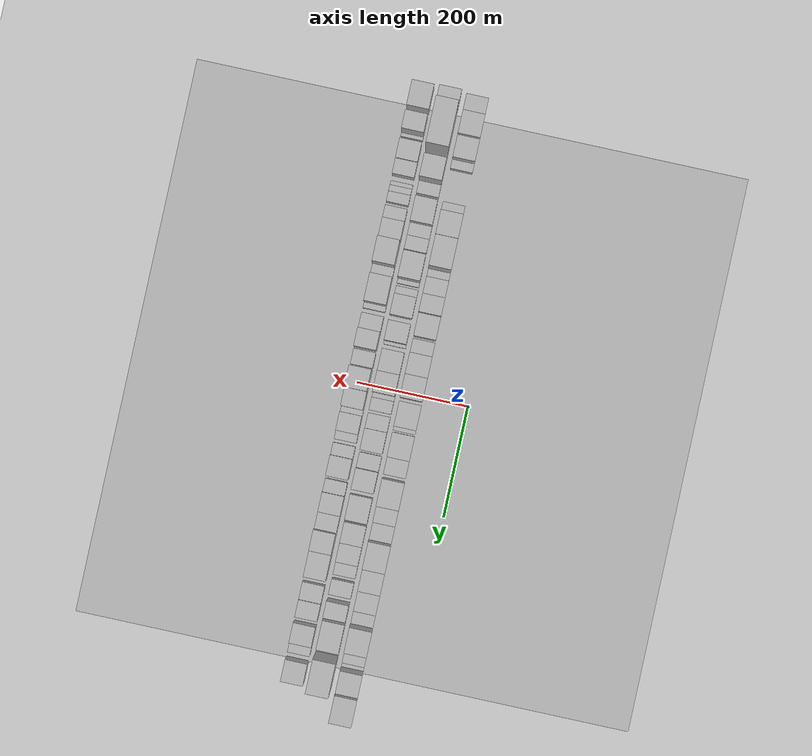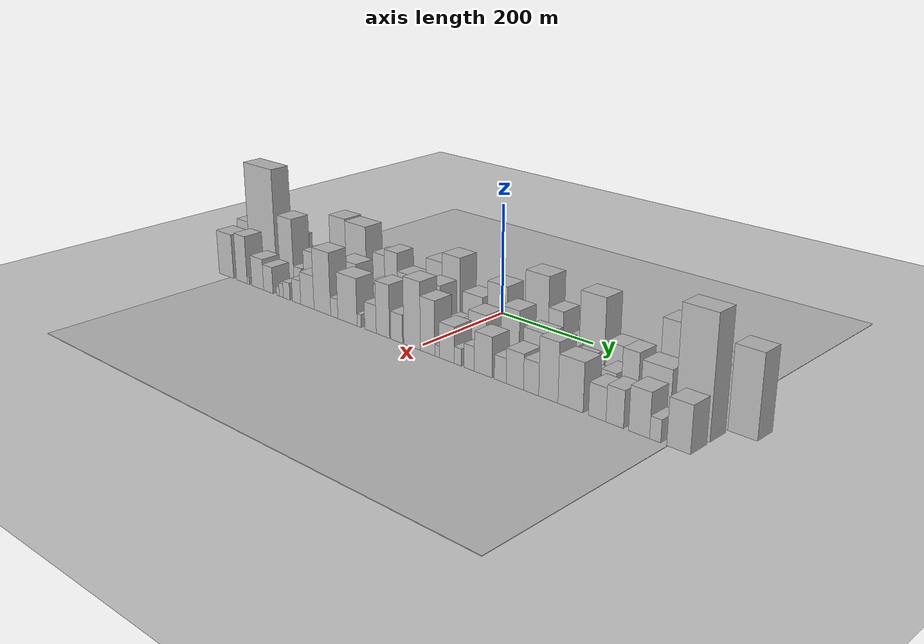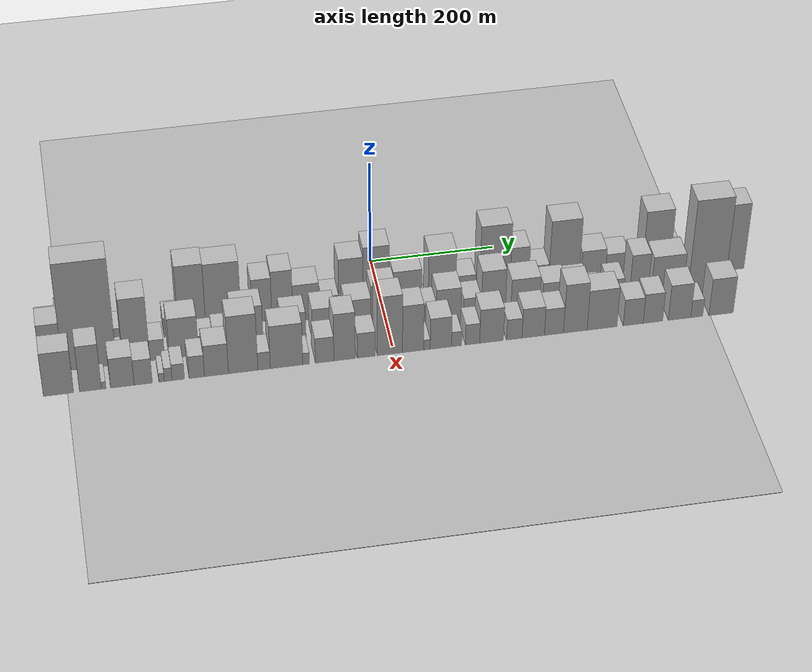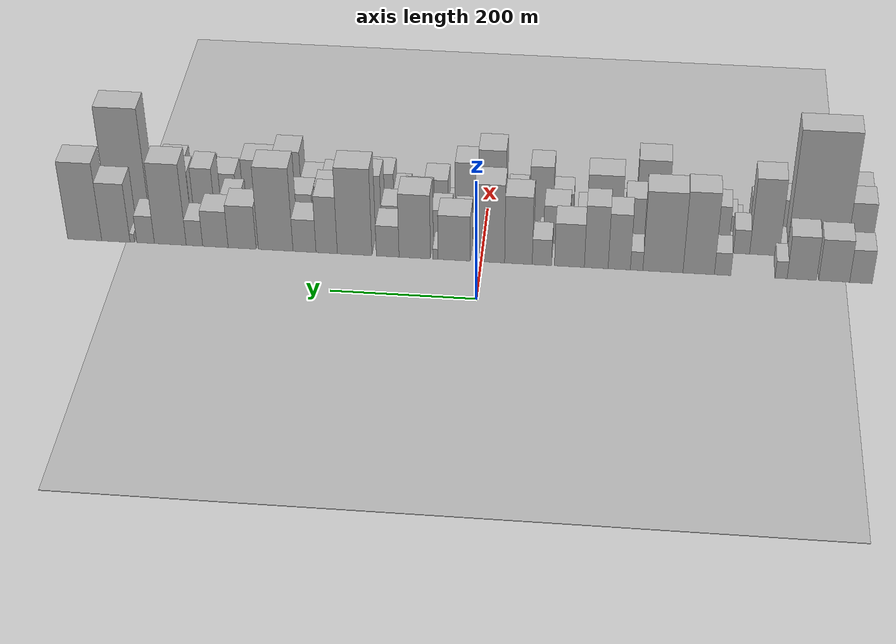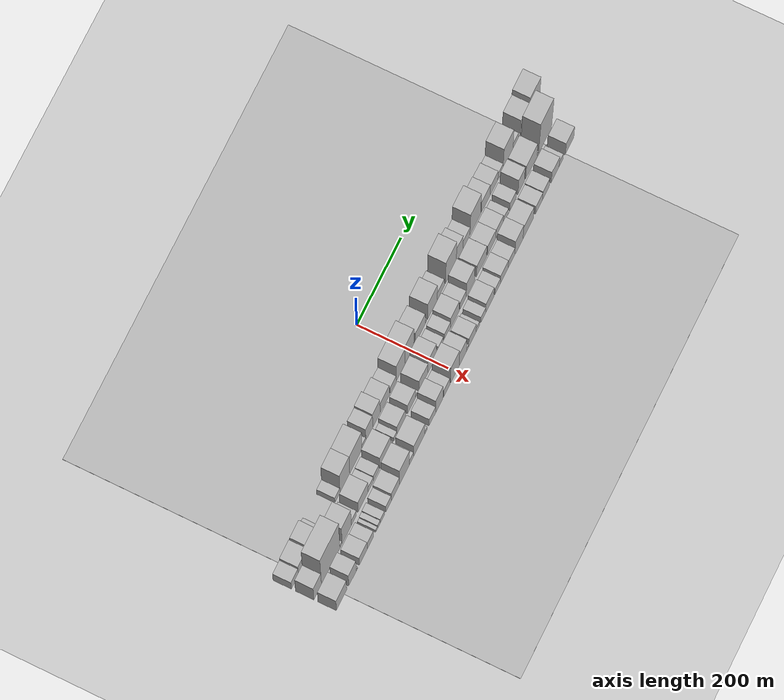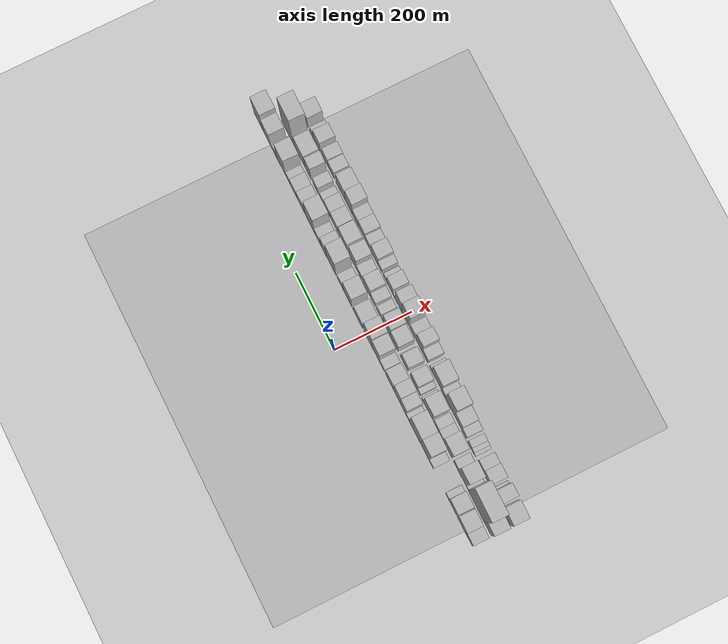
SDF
<?xml version="1.0" encoding="utf-8"?>

<sdf version="1.6">

   <world name="default">

      <gui fullscreen="0">

         <camera name="user_camera">

            <pose>-15 0 4.57585 0 0 0</pose>

            <view_controller>orbit</view_controller>

         </camera>

      </gui>

      <scene>

         <sky>

           <clouds>

             <speed>12</speed>

           </clouds>

         </sky>

         <ambient>0.4 0.4 0.4 1</ambient>

         <background>0.7 0.7 0.7 1</background>

         <shadows>1</shadows>

      </scene>

      <gravity>0 0 -9.8066</gravity>

      <magnetic_field>6e-06 2.3e-05 -4.2e-05</magnetic_field>

      <physics default="0" name="default_physics" type="ode">

         <ode>

            <solver>

               <type>quick</type>

               <iters>10</iters>

               <sor>1.0</sor>

               <use_dynamic_moi_rescaling>0</use_dynamic_moi_rescaling>

            </solver>

            <constraints>

               <cfm>0</cfm>

               <erp>0.2</erp>

               <contact_max_correcting_vel>100</contact_max_correcting_vel>

               <contact_surface_layer>0.001</contact_surface_layer>

            </constraints>

         </ode>

         <max_step_size>0.004</max_step_size>

         <real_time_factor>1</real_time_factor>

         <real_time_update_rate>250</real_time_update_rate>

      </physics>

      <light name="sun" type="directional">

         <cast_shadows>1</cast_shadows>

         <pose>0 0 10 0 0 0</pose>

         <diffuse>0.8 0.8 0.8 1</diffuse>

         <specular>0.2 0.2 0.2 1</specular>

         <attenuation>

            <range>1000</range>

            <constant>0.9</constant>

            <linear>0.01</linear>

            <quadratic>0.001</quadratic>

         </attenuation>

         <direction>-0.5 0.1 -0.9</direction>

      </light>

      <include>

         <name>ground_plane_1</name>

         <uri>model://HANNAS_ground_plane</uri>

         <pose>0 0 0  0 0 0</pose>

      </include>

      <include>

         <name>ground_plane_2</name>

         <uri>model://HANNAS_ground_plane</uri>

         <pose>100 0 0  0 0 0</pose>

      </include>

      <model name="building_1">

         <static>1</static>

         <pose frame="">100.0000 -520.7160 0 0.000000 0.000000 0.000000</pose>

         <link name="link">

            <pose frame="">0 0 28.50 0 0 0</pose>

            <collision name="collision">

               <geometry>

                  <box>

                     <size>40.0000 30.5679 57.0000</size>

                  </box>

               </geometry>

               <max_contacts>10</max_contacts>

               <surface>

                  <contact>

                     <ode/>

                  </contact>

                  <bounce/>

                  <friction>

                     <torsional>

                        <ode/>

                     </torsional>

                     <ode/>

                  </friction>

               </surface>

            </collision>

            <visual name="visual">

               <cast_shadows>0</cast_shadows>

               <geometry>

                  <box>

                     <size>40.0000 30.5679 57.0000</size>

                  </box>

               </geometry>

               <material>

                  <script>

                     <uri>model://HANNAS_wall/materials/scripts</uri>

                     <uri>model://HANNAS_wall/materials/textures</uri>

                     <name>vrc/HANNAS_wall</name>

                  </script>

               </material>

            </visual>

            <self_collide>0</self_collide>

            <enable_wind>0</enable_wind>

            <kinematic>0</kinematic>

         </link>

      </model>

      <model name="building_2">

         <static>1</static>

         <pose frame="">100.0000 -484.4016 0 0.000000 0.000000 0.000000</pose>

         <link name="link">

            <pose frame="">0 0 36.00 0 0 0</pose>

            <collision name="collision">

               <geometry>

                  <box>

                     <size>40.0000 42.0609 72.0000</size>

                  </box>

               </geometry>

               <max_contacts>10</max_contacts>

               <surface>

                  <contact>

                     <ode/>

                  </contact>

                  <bounce/>

                  <friction>

                     <torsional>

                        <ode/>

                     </torsional>

                     <ode/>

                  </friction>

               </surface>

            </collision>

            <visual name="visual">

               <cast_shadows>0</cast_shadows>

               <geometry>

                  <box>

                     <size>40.0000 42.0609 72.0000</size>

                  </box>

               </geometry>

               <material>

                  <script>

                     <uri>model://HANNAS_wall/materials/scripts</uri>

                     <uri>model://HANNAS_wall/materials/textures</uri>

                     <name>vrc/HANNAS_wall</name>

                  </script>

               </material>

            </visual>

            <self_collide>0</self_collide>

            <enable_wind>0</enable_wind>

            <kinematic>0</kinematic>

         </link>

      </model>

      <model name="building_3">

         <static>1</static>

         <pose frame="">100.0000 -440.3986 0 0.000000 0.000000 0.000000</pose>

         <link name="link">

            <pose frame="">0 0 37.50 0 0 0</pose>

            <collision name="collision">

               <geometry>

                  <box>

                     <size>40.0000 39.9451 75.0000</size>

                  </box>

               </geometry>

               <max_contacts>10</max_contacts>

               <surface>

                  <contact>

                     <ode/>

                  </contact>

                  <bounce/>

                  <friction>

                     <torsional>

                        <ode/>

                     </torsional>

                     <ode/>

                  </friction>

               </surface>

            </collision>

            <visual name="visual">

               <cast_shadows>0</cast_shadows>

               <geometry>

                  <box>

                     <size>40.0000 39.9451 75.0000</size>

                  </box>

               </geometry>

               <material>

                  <script>

                     <uri>model://HANNAS_wall/materials/scripts</uri>

                     <uri>model://HANNAS_wall/materials/textures</uri>

                     <name>vrc/HANNAS_wall</name>

                  </script>

               </material>

            </visual>

            <self_collide>0</self_collide>

            <enable_wind>0</enable_wind>

            <kinematic>0</kinematic>

         </link>

      </model>

      <model name="building_4">

         <static>1</static>

         <pose frame="">100.0000 -412.2053 0 0.000000 0.000000 0.000000</pose>

         <link name="link">

            <pose frame="">0 0 15.00 0 0 0</pose>

            <collision name="collision">

               <geometry>

                  <box>

                     <size>40.0000 16.4415 30.0000</size>

                  </box>

               </geometry>

               <max_contacts>10</max_contacts>

               <surface>

                  <contact>

                     <ode/>

                  </contact>

                  <bounce/>

                  <friction>

                     <torsional>

                        <ode/>

                     </torsional>

                     <ode/>

                  </friction>

               </surface>

            </collision>

            <visual name="visual">

               <cast_shadows>0</cast_shadows>

               <geometry>

                  <box>

                     <size>40.0000 16.4415 30.0000</size>

                  </box>

               </geometry>

               <material>

                  <script>

                     <uri>model://HANNAS_wall/materials/scripts</uri>

                     <uri>model://HANNAS_wall/materials/textures</uri>

                     <name>vrc/HANNAS_wall</name>

                  </script>

               </material>

            </visual>

            <self_collide>0</self_collide>

            <enable_wind>0</enable_wind>

            <kinematic>0</kinematic>

         </link>

      </model>

      <model name="building_5">

         <static>1</static>

         <pose frame="">100.0000 -332.3766 0 0.000000 0.000000 0.000000</pose>

         <link name="link">

            <pose frame="">0 0 19.50 0 0 0</pose>

            <collision name="collision">

               <geometry>

                  <box>

                     <size>40.0000 22.4053 39.0000</size>

                  </box>

               </geometry>

               <max_contacts>10</max_contacts>

               <surface>

                  <contact>

                     <ode/>

                  </contact>

                  <bounce/>

                  <friction>

                     <torsional>

                        <ode/>

                     </torsional>

                     <ode/>

                  </friction>

               </surface>

            </collision>

            <visual name="visual">

               <cast_shadows>0</cast_shadows>

               <geometry>

                  <box>

                     <size>40.0000 22.4053 39.0000</size>

                  </box>

               </geometry>

               <material>

                  <script>

                     <uri>model://HANNAS_wall/materials/scripts</uri>

                     <uri>model://HANNAS_wall/materials/textures</uri>

                     <name>vrc/HANNAS_wall</name>

                  </script>

               </material>

            </visual>

            <self_collide>0</self_collide>

            <enable_wind>0</enable_wind>

            <kinematic>0</kinematic>

         </link>

      </model>

      <model name="building_6">

         <static>1</static>

         <pose frame="">100.0000 -299.6409 0 0.000000 0.000000 0.000000</pose>

         <link name="link">

            <pose frame="">0 0 70.50 0 0 0</pose>

            <collision name="collision">

               <geometry>

                  <box>

                     <size>40.0000 43.0661 141.0000</size>

                  </box>

               </geometry>

               <max_contacts>10</max_contacts>

               <surface>

                  <contact>

                     <ode/>

                  </contact>

                  <bounce/>

                  <friction>

                     <torsional>

                        <ode/>

                     </torsional>

                     <ode/>

                  </friction>

               </surface>

            </collision>

            <visual name="visual">

               <cast_shadows>0</cast_shadows>

               <geometry>

                  <box>

                     <size>40.0000 43.0661 141.0000</size>

                  </box>

               </geometry>

               <material>

                  <script>

                     <uri>model://HANNAS_wall/materials/scripts</uri>

                     <uri>model://HANNAS_wall/materials/textures</uri>

                     <name>vrc/HANNAS_wall</name>

                  </script>

               </material>

            </visual>

            <self_collide>0</self_collide>

            <enable_wind>0</enable_wind>

            <kinematic>0</kinematic>

         </link>

      </model>

      <model name="building_7">

         <static>1</static>

         <pose frame="">100.0000 -250.5822 0 0.000000 0.000000 0.000000</pose>

         <link name="link">

            <pose frame="">0 0 69.00 0 0 0</pose>

            <collision name="collision">

               <geometry>

                  <box>

                     <size>40.0000 55.0513 138.0000</size>

                  </box>

               </geometry>

               <max_contacts>10</max_contacts>

               <surface>

                  <contact>

                     <ode/>

                  </contact>

                  <bounce/>

                  <friction>

                     <torsional>

                        <ode/>

                     </torsional>

                     <ode/>

                  </friction>

               </surface>

            </collision>

            <visual name="visual">

               <cast_shadows>0</cast_shadows>

               <geometry>

                  <box>

                     <size>40.0000 55.0513 138.0000</size>

                  </box>

               </geometry>

               <material>

                  <script>

                     <uri>model://HANNAS_wall/materials/scripts</uri>

                     <uri>model://HANNAS_wall/materials/textures</uri>

                     <name>vrc/HANNAS_wall</name>

                  </script>

               </material>

            </visual>

            <self_collide>0</self_collide>

            <enable_wind>0</enable_wind>

            <kinematic>0</kinematic>

         </link>

      </model>

      <model name="building_8">

         <static>1</static>

         <pose frame="">100.0000 -214.4647 0 0.000000 0.000000 0.000000</pose>

         <link name="link">

            <pose frame="">0 0 16.50 0 0 0</pose>

            <collision name="collision">

               <geometry>

                  <box>

                     <size>40.0000 17.1836 33.0000</size>

                  </box>

               </geometry>

               <max_contacts>10</max_contacts>

               <surface>

                  <contact>

                     <ode/>

                  </contact>

                  <bounce/>

                  <friction>

                     <torsional>

                        <ode/>

                     </torsional>

                     <ode/>

                  </friction>

               </surface>

            </collision>

            <visual name="visual">

               <cast_shadows>0</cast_shadows>

               <geometry>

                  <box>

                     <size>40.0000 17.1836 33.0000</size>

                  </box>

               </geometry>

               <material>

                  <script>

                     <uri>model://HANNAS_wall/materials/scripts</uri>

                     <uri>model://HANNAS_wall/materials/textures</uri>

                     <name>vrc/HANNAS_wall</name>

                  </script>

               </material>

            </visual>

            <self_collide>0</self_collide>

            <enable_wind>0</enable_wind>

            <kinematic>0</kinematic>

         </link>

      </model>

      <model name="building_9">

         <static>1</static>

         <pose frame="">100.0000 -190.5602 0 0.000000 0.000000 0.000000</pose>

         <link name="link">

            <pose frame="">0 0 48.00 0 0 0</pose>

            <collision name="collision">

               <geometry>

                  <box>

                     <size>40.0000 30.6254 96.0000</size>

                  </box>

               </geometry>

               <max_contacts>10</max_contacts>

               <surface>

                  <contact>

                     <ode/>

                  </contact>

                  <bounce/>

                  <friction>

                     <torsional>

                        <ode/>

                     </torsional>

                     <ode/>

                  </friction>

               </surface>

            </collision>

            <visual name="visual">

               <cast_shadows>0</cast_shadows>

               <geometry>

                  <box>

                     <size>40.0000 30.6254 96.0000</size>

                  </box>

               </geometry>

               <material>

                  <script>

                     <uri>model://HANNAS_wall/materials/scripts</uri>

                     <uri>model://HANNAS_wall/materials/textures</uri>

                     <name>vrc/HANNAS_wall</name>

                  </script>

               </material>

            </visual>

            <self_collide>0</self_collide>

            <enable_wind>0</enable_wind>

            <kinematic>0</kinematic>

         </link>

      </model>

      <model name="building_10">

         <static>1</static>

         <pose frame="">100.0000 -158.8489 0 0.000000 0.000000 0.000000</pose>

         <link name="link">

            <pose frame="">0 0 54.00 0 0 0</pose>

            <collision name="collision">

               <geometry>

                  <box>

                     <size>40.0000 32.7972 108.0000</size>

                  </box>

               </geometry>

               <max_contacts>10</max_contacts>

               <surface>

                  <contact>

                     <ode/>

                  </contact>

                  <bounce/>

                  <friction>

                     <torsional>

                        <ode/>

                     </torsional>

                     <ode/>

                  </friction>

               </surface>

            </collision>

            <visual name="visual">

               <cast_shadows>0</cast_shadows>

               <geometry>

                  <box>

                     <size>40.0000 32.7972 108.0000</size>

                  </box>

               </geometry>

               <material>

                  <script>

                     <uri>model://HANNAS_wall/materials/scripts</uri>

                     <uri>model://HANNAS_wall/materials/textures</uri>

                     <name>vrc/HANNAS_wall</name>

                  </script>

               </material>

            </visual>

            <self_collide>0</self_collide>

            <enable_wind>0</enable_wind>

            <kinematic>0</kinematic>

         </link>

      </model>

      <model name="building_11">

         <static>1</static>

         <pose frame="">100.0000 -121.7645 0 0.000000 0.000000 0.000000</pose>

         <link name="link">

            <pose frame="">0 0 37.50 0 0 0</pose>

            <collision name="collision">

               <geometry>

                  <box>

                     <size>40.0000 41.3716 75.0000</size>

                  </box>

               </geometry>

               <max_contacts>10</max_contacts>

               <surface>

                  <contact>

                     <ode/>

                  </contact>

                  <bounce/>

                  <friction>

                     <torsional>

                        <ode/>

                     </torsional>

                     <ode/>

                  </friction>

               </surface>

            </collision>

            <visual name="visual">

               <cast_shadows>0</cast_shadows>

               <geometry>

                  <box>

                     <size>40.0000 41.3716 75.0000</size>

                  </box>

               </geometry>

               <material>

                  <script>

                     <uri>model://HANNAS_wall/materials/scripts</uri>

                     <uri>model://HANNAS_wall/materials/textures</uri>

                     <name>vrc/HANNAS_wall</name>

                  </script>

               </material>

            </visual>

            <self_collide>0</self_collide>

            <enable_wind>0</enable_wind>

            <kinematic>0</kinematic>

         </link>

      </model>

      <model name="building_12">

         <static>1</static>

         <pose frame="">100.0000 -83.7302 0 0.000000 0.000000 0.000000</pose>

         <link name="link">

            <pose frame="">0 0 22.50 0 0 0</pose>

            <collision name="collision">

               <geometry>

                  <box>

                     <size>40.0000 26.6971 45.0000</size>

                  </box>

               </geometry>

               <max_contacts>10</max_contacts>

               <surface>

                  <contact>

                     <ode/>

                  </contact>

                  <bounce/>

                  <friction>

                     <torsional>

                        <ode/>

                     </torsional>

                     <ode/>

                  </friction>

               </surface>

            </collision>

            <visual name="visual">

               <cast_shadows>0</cast_shadows>

               <geometry>

                  <box>

                     <size>40.0000 26.6971 45.0000</size>

                  </box>

               </geometry>

               <material>

                  <script>

                     <uri>model://HANNAS_wall/materials/scripts</uri>

                     <uri>model://HANNAS_wall/materials/textures</uri>

                     <name>vrc/HANNAS_wall</name>

                  </script>

               </material>

            </visual>

            <self_collide>0</self_collide>

            <enable_wind>0</enable_wind>

            <kinematic>0</kinematic>

         </link>

      </model>

      <model name="building_13">

         <static>1</static>

         <pose frame="">100.0000 -51.2228 0 0.000000 0.000000 0.000000</pose>

         <link name="link">

            <pose frame="">0 0 58.50 0 0 0</pose>

            <collision name="collision">

               <geometry>

                  <box>

                     <size>40.0000 38.3178 117.0000</size>

                  </box>

               </geometry>

               <max_contacts>10</max_contacts>

               <surface>

                  <contact>

                     <ode/>

                  </contact>

                  <bounce/>

                  <friction>

                     <torsional>

                        <ode/>

                     </torsional>

                     <ode/>

                  </friction>

               </surface>

            </collision>

            <visual name="visual">

               <cast_shadows>0</cast_shadows>

               <geometry>

                  <box>

                     <size>40.0000 38.3178 117.0000</size>

                  </box>

               </geometry>

               <material>

                  <script>

                     <uri>model://HANNAS_wall/materials/scripts</uri>

                     <uri>model://HANNAS_wall/materials/textures</uri>

                     <name>vrc/HANNAS_wall</name>

                  </script>

               </material>

            </visual>

            <self_collide>0</self_collide>

            <enable_wind>0</enable_wind>

            <kinematic>0</kinematic>

         </link>

      </model>

      <model name="building_14">

         <static>1</static>

         <pose frame="">100.0000 -11.2822 0 0.000000 0.000000 0.000000</pose>

         <link name="link">

            <pose frame="">0 0 67.50 0 0 0</pose>

            <collision name="collision">

               <geometry>

                  <box>

                     <size>40.0000 41.5633 135.0000</size>

                  </box>

               </geometry>

               <max_contacts>10</max_contacts>

               <surface>

                  <contact>

                     <ode/>

                  </contact>

                  <bounce/>

                  <friction>

                     <torsional>

                        <ode/>

                     </torsional>

                     <ode/>

                  </friction>

               </surface>

            </collision>

            <visual name="visual">

               <cast_shadows>0</cast_shadows>

               <geometry>

                  <box>

                     <size>40.0000 41.5633 135.0000</size>

                  </box>

               </geometry>

               <material>

                  <script>

                     <uri>model://HANNAS_wall/materials/scripts</uri>

                     <uri>model://HANNAS_wall/materials/textures</uri>

                     <name>vrc/HANNAS_wall</name>

                  </script>

               </material>

            </visual>

            <self_collide>0</self_collide>

            <enable_wind>0</enable_wind>

            <kinematic>0</kinematic>

         </link>

      </model>

      <model name="building_15">

         <static>1</static>

         <pose frame="">100.0000 37.9918 0 0.000000 0.000000 0.000000</pose>

         <link name="link">

            <pose frame="">0 0 39.00 0 0 0</pose>

            <collision name="collision">

               <geometry>

                  <box>

                     <size>40.0000 44.9849 78.0000</size>

                  </box>

               </geometry>

               <max_contacts>10</max_contacts>

               <surface>

                  <contact>

                     <ode/>

                  </contact>

                  <bounce/>

                  <friction>

                     <torsional>

                        <ode/>

                     </torsional>

                     <ode/>

                  </friction>

               </surface>

            </collision>

            <visual name="visual">

               <cast_shadows>0</cast_shadows>

               <geometry>

                  <box>

                     <size>40.0000 44.9849 78.0000</size>

                  </box>

               </geometry>

               <material>

                  <script>

                     <uri>model://HANNAS_wall/materials/scripts</uri>

                     <uri>model://HANNAS_wall/materials/textures</uri>

                     <name>vrc/HANNAS_wall</name>

                  </script>

               </material>

            </visual>

            <self_collide>0</self_collide>

            <enable_wind>0</enable_wind>

            <kinematic>0</kinematic>

         </link>

      </model>

      <model name="building_16">

         <static>1</static>

         <pose frame="">100.0000 64.3034 0 0.000000 0.000000 0.000000</pose>

         <link name="link">

            <pose frame="">0 0 9.00 0 0 0</pose>

            <collision name="collision">

               <geometry>

                  <box>

                     <size>40.0000 7.6383 18.0000</size>

                  </box>

               </geometry>

               <max_contacts>10</max_contacts>

               <surface>

                  <contact>

                     <ode/>

                  </contact>

                  <bounce/>

                  <friction>

                     <torsional>

                        <ode/>

                     </torsional>

                     <ode/>

                  </friction>

               </surface>

            </collision>

            <visual name="visual">

               <cast_shadows>0</cast_shadows>

               <geometry>

                  <box>

                     <size>40.0000 7.6383 18.0000</size>

                  </box>

               </geometry>

               <material>

                  <script>

                     <uri>model://HANNAS_wall/materials/scripts</uri>

                     <uri>model://HANNAS_wall/materials/textures</uri>

                     <name>vrc/HANNAS_wall</name>

                  </script>

               </material>

            </visual>

            <self_collide>0</self_collide>

            <enable_wind>0</enable_wind>

            <kinematic>0</kinematic>

         </link>

      </model>

      <model name="building_17">

         <static>1</static>

         <pose frame="">100.0000 93.0453 0 0.000000 0.000000 0.000000</pose>

         <link name="link">

            <pose frame="">0 0 55.50 0 0 0</pose>

            <collision name="collision">

               <geometry>

                  <box>

                     <size>40.0000 43.8455 111.0000</size>

                  </box>

               </geometry>

               <max_contacts>10</max_contacts>

               <surface>

                  <contact>

                     <ode/>

                  </contact>

                  <bounce/>

                  <friction>

                     <torsional>

                        <ode/>

                     </torsional>

                     <ode/>

                  </friction>

               </surface>

            </collision>

            <visual name="visual">

               <cast_shadows>0</cast_shadows>

               <geometry>

                  <box>

                     <size>40.0000 43.8455 111.0000</size>

                  </box>

               </geometry>

               <material>

                  <script>

                     <uri>model://HANNAS_wall/materials/scripts</uri>

                     <uri>model://HANNAS_wall/materials/textures</uri>

                     <name>vrc/HANNAS_wall</name>

                  </script>

               </material>

            </visual>

            <self_collide>0</self_collide>

            <enable_wind>0</enable_wind>

            <kinematic>0</kinematic>

         </link>

      </model>

      <model name="building_18">

         <static>1</static>

         <pose frame="">100.0000 130.8705 0 0.000000 0.000000 0.000000</pose>

         <link name="link">

            <pose frame="">0 0 27.00 0 0 0</pose>

            <collision name="collision">

               <geometry>

                  <box>

                     <size>40.0000 31.8048 54.0000</size>

                  </box>

               </geometry>

               <max_contacts>10</max_contacts>

               <surface>

                  <contact>

                     <ode/>

                  </contact>

                  <bounce/>

                  <friction>

                     <torsional>

                        <ode/>

                     </torsional>

                     <ode/>

                  </friction>

               </surface>

            </collision>

            <visual name="visual">

               <cast_shadows>0</cast_shadows>

               <geometry>

                  <box>

                     <size>40.0000 31.8048 54.0000</size>

                  </box>

               </geometry>

               <material>

                  <script>

                     <uri>model://HANNAS_wall/materials/scripts</uri>

                     <uri>model://HANNAS_wall/materials/textures</uri>

                     <name>vrc/HANNAS_wall</name>

                  </script>

               </material>

            </visual>

            <self_collide>0</self_collide>

            <enable_wind>0</enable_wind>

            <kinematic>0</kinematic>

         </link>

      </model>

      <model name="building_19">

         <static>1</static>

         <pose frame="">100.0000 177.0895 0 0.000000 0.000000 0.000000</pose>

         <link name="link">

            <pose frame="">0 0 75.00 0 0 0</pose>

            <collision name="collision">

               <geometry>

                  <box>

                     <size>40.0000 48.6332 150.0000</size>

                  </box>

               </geometry>

               <max_contacts>10</max_contacts>

               <surface>

                  <contact>

                     <ode/>

                  </contact>

                  <bounce/>

                  <friction>

                     <torsional>

                        <ode/>

                     </torsional>

                     <ode/>

                  </friction>

               </surface>

            </collision>

            <visual name="visual">

               <cast_shadows>0</cast_shadows>

               <geometry>

                  <box>

                     <size>40.0000 48.6332 150.0000</size>

                  </box>

               </geometry>

               <material>

                  <script>

                     <uri>model://HANNAS_wall/materials/scripts</uri>

                     <uri>model://HANNAS_wall/materials/textures</uri>

                     <name>vrc/HANNAS_wall</name>

                  </script>

               </material>

            </visual>

            <self_collide>0</self_collide>

            <enable_wind>0</enable_wind>

            <kinematic>0</kinematic>

         </link>

      </model>

      <model name="building_20">

         <static>1</static>

         <pose frame="">100.0000 216.3856 0 0.000000 0.000000 0.000000</pose>

         <link name="link">

            <pose frame="">0 0 49.50 0 0 0</pose>

            <collision name="collision">

               <geometry>

                  <box>

                     <size>40.0000 29.9591 99.0000</size>

                  </box>

               </geometry>

               <max_contacts>10</max_contacts>

               <surface>

                  <contact>

                     <ode/>

                  </contact>

                  <bounce/>

                  <friction>

                     <torsional>

                        <ode/>

                     </torsional>

                     <ode/>

                  </friction>

               </surface>

            </collision>

            <visual name="visual">

               <cast_shadows>0</cast_shadows>

               <geometry>

                  <box>

                     <size>40.0000 29.9591 99.0000</size>

                  </box>

               </geometry>

               <material>

                  <script>

                     <uri>model://HANNAS_wall/materials/scripts</uri>

                     <uri>model://HANNAS_wall/materials/textures</uri>

                     <name>vrc/HANNAS_wall</name>

                  </script>

               </material>

            </visual>

            <self_collide>0</self_collide>

            <enable_wind>0</enable_wind>

            <kinematic>0</kinematic>

         </link>

      </model>

      <model name="building_21">

         <static>1</static>

         <pose frame="">100.0000 247.5497 0 0.000000 0.000000 0.000000</pose>

         <link name="link">

            <pose frame="">0 0 28.50 0 0 0</pose>

            <collision name="collision">

               <geometry>

                  <box>

                     <size>40.0000 32.3690 57.0000</size>

                  </box>

               </geometry>

               <max_contacts>10</max_contacts>

               <surface>

                  <contact>

                     <ode/>

                  </contact>

                  <bounce/>

                  <friction>

                     <torsional>

                        <ode/>

                     </torsional>

                     <ode/>

                  </friction>

               </surface>

            </collision>

            <visual name="visual">

               <cast_shadows>0</cast_shadows>

               <geometry>

                  <box>

                     <size>40.0000 32.3690 57.0000</size>

                  </box>

               </geometry>

               <material>

                  <script>

                     <uri>model://HANNAS_wall/materials/scripts</uri>

                     <uri>model://HANNAS_wall/materials/textures</uri>

                     <name>vrc/HANNAS_wall</name>

                  </script>

               </material>

            </visual>

            <self_collide>0</self_collide>

            <enable_wind>0</enable_wind>

            <kinematic>0</kinematic>

         </link>

      </model>

      <model name="building_22">

         <static>1</static>

         <pose frame="">100.0000 288.2058 0 0.000000 0.000000 0.000000</pose>

         <link name="link">

            <pose frame="">0 0 72.00 0 0 0</pose>

            <collision name="collision">

               <geometry>

                  <box>

                     <size>40.0000 48.9432 144.0000</size>

                  </box>

               </geometry>

               <max_contacts>10</max_contacts>

               <surface>

                  <contact>

                     <ode/>

                  </contact>

                  <bounce/>

                  <friction>

                     <torsional>

                        <ode/>

                     </torsional>

                     <ode/>

                  </friction>

               </surface>

            </collision>

            <visual name="visual">

               <cast_shadows>0</cast_shadows>

               <geometry>

                  <box>

                     <size>40.0000 48.9432 144.0000</size>

                  </box>

               </geometry>

               <material>

                  <script>

                     <uri>model://HANNAS_wall/materials/scripts</uri>

                     <uri>model://HANNAS_wall/materials/textures</uri>

                     <name>vrc/HANNAS_wall</name>

                  </script>

               </material>

            </visual>

            <self_collide>0</self_collide>

            <enable_wind>0</enable_wind>

            <kinematic>0</kinematic>

         </link>

      </model>

      <model name="building_23">

         <static>1</static>

         <pose frame="">100.0000 335.4742 0 0.000000 0.000000 0.000000</pose>

         <link name="link">

            <pose frame="">0 0 37.50 0 0 0</pose>

            <collision name="collision">

               <geometry>

                  <box>

                     <size>40.0000 39.5936 75.0000</size>

                  </box>

               </geometry>

               <max_contacts>10</max_contacts>

               <surface>

                  <contact>

                     <ode/>

                  </contact>

                  <bounce/>

                  <friction>

                     <torsional>

                        <ode/>

                     </torsional>

                     <ode/>

                  </friction>

               </surface>

            </collision>

            <visual name="visual">

               <cast_shadows>0</cast_shadows>

               <geometry>

                  <box>

                     <size>40.0000 39.5936 75.0000</size>

                  </box>

               </geometry>

               <material>

                  <script>

                     <uri>model://HANNAS_wall/materials/scripts</uri>

                     <uri>model://HANNAS_wall/materials/textures</uri>

                     <name>vrc/HANNAS_wall</name>

                  </script>

               </material>

            </visual>

            <self_collide>0</self_collide>

            <enable_wind>0</enable_wind>

            <kinematic>0</kinematic>

         </link>

      </model>

      <model name="building_24">

         <static>1</static>

         <pose frame="">100.0000 373.3319 0 0.000000 0.000000 0.000000</pose>

         <link name="link">

            <pose frame="">0 0 31.50 0 0 0</pose>

            <collision name="collision">

               <geometry>

                  <box>

                     <size>40.0000 36.1218 63.0000</size>

                  </box>

               </geometry>

               <max_contacts>10</max_contacts>

               <surface>

                  <contact>

                     <ode/>

                  </contact>

                  <bounce/>

                  <friction>

                     <torsional>

                        <ode/>

                     </torsional>

                     <ode/>

                  </friction>

               </surface>

            </collision>

            <visual name="visual">

               <cast_shadows>0</cast_shadows>

               <geometry>

                  <box>

                     <size>40.0000 36.1218 63.0000</size>

                  </box>

               </geometry>

               <material>

                  <script>

                     <uri>model://HANNAS_wall/materials/scripts</uri>

                     <uri>model://HANNAS_wall/materials/textures</uri>

                     <name>vrc/HANNAS_wall</name>

                  </script>

               </material>

            </visual>

            <self_collide>0</self_collide>

            <enable_wind>0</enable_wind>

            <kinematic>0</kinematic>

         </link>

      </model>

      <model name="building_25">

         <static>1</static>

         <pose frame="">100.0000 403.0657 0 0.000000 0.000000 0.000000</pose>

         <link name="link">

            <pose frame="">0 0 22.50 0 0 0</pose>

            <collision name="collision">

               <geometry>

                  <box>

                     <size>40.0000 23.3459 45.0000</size>

                  </box>

               </geometry>

               <max_contacts>10</max_contacts>

               <surface>

                  <contact>

                     <ode/>

                  </contact>

                  <bounce/>

                  <friction>

                     <torsional>

                        <ode/>

                     </torsional>

                     <ode/>

                  </friction>

               </surface>

            </collision>

            <visual name="visual">

               <cast_shadows>0</cast_shadows>

               <geometry>

                  <box>

                     <size>40.0000 23.3459 45.0000</size>

                  </box>

               </geometry>

               <material>

                  <script>

                     <uri>model://HANNAS_wall/materials/scripts</uri>

                     <uri>model://HANNAS_wall/materials/textures</uri>

                     <name>vrc/HANNAS_wall</name>

                  </script>

               </material>

            </visual>

            <self_collide>0</self_collide>

            <enable_wind>0</enable_wind>

            <kinematic>0</kinematic>

         </link>

      </model>

      <model name="building_26">

         <static>1</static>

         <pose frame="">100.0000 437.3186 0 0.000000 0.000000 0.000000</pose>

         <link name="link">

            <pose frame="">0 0 70.50 0 0 0</pose>

            <collision name="collision">

               <geometry>

                  <box>

                     <size>40.0000 45.1599 141.0000</size>

                  </box>

               </geometry>

               <max_contacts>10</max_contacts>

               <surface>

                  <contact>

                     <ode/>

                  </contact>

                  <bounce/>

                  <friction>

                     <torsional>

                        <ode/>

                     </torsional>

                     <ode/>

                  </friction>

               </surface>

            </collision>

            <visual name="visual">

               <cast_shadows>0</cast_shadows>

               <geometry>

                  <box>

                     <size>40.0000 45.1599 141.0000</size>

                  </box>

               </geometry>

               <material>

                  <script>

                     <uri>model://HANNAS_wall/materials/scripts</uri>

                     <uri>model://HANNAS_wall/materials/textures</uri>

                     <name>vrc/HANNAS_wall</name>

                  </script>

               </material>

            </visual>

            <self_collide>0</self_collide>

            <enable_wind>0</enable_wind>

            <kinematic>0</kinematic>

         </link>

      </model>

      <model name="building_27">

         <static>1</static>

         <pose frame="">100.0000 472.4783 0 0.000000 0.000000 0.000000</pose>

         <link name="link">

            <pose frame="">0 0 24.00 0 0 0</pose>

            <collision name="collision">

               <geometry>

                  <box>

                     <size>40.0000 25.1595 48.0000</size>

                  </box>

               </geometry>

               <max_contacts>10</max_contacts>

               <surface>

                  <contact>

                     <ode/>

                  </contact>

                  <bounce/>

                  <friction>

                     <torsional>

                        <ode/>

                     </torsional>

                     <ode/>

                  </friction>

               </surface>

            </collision>

            <visual name="visual">

               <cast_shadows>0</cast_shadows>

               <geometry>

                  <box>

                     <size>40.0000 25.1595 48.0000</size>

                  </box>

               </geometry>

               <material>

                  <script>

                     <uri>model://HANNAS_wall/materials/scripts</uri>

                     <uri>model://HANNAS_wall/materials/textures</uri>

                     <name>vrc/HANNAS_wall</name>

                  </script>

               </material>

            </visual>

            <self_collide>0</self_collide>

            <enable_wind>0</enable_wind>

            <kinematic>0</kinematic>

         </link>

      </model>

      <model name="building_28">

         <static>1</static>

         <pose frame="">100.0000 491.3182 0 0.000000 0.000000 0.000000</pose>

         <link name="link">

            <pose frame="">0 0 7.50 0 0 0</pose>

            <collision name="collision">

               <geometry>

                  <box>

                     <size>40.0000 6.5202 15.0000</size>

                  </box>

               </geometry>

               <max_contacts>10</max_contacts>

               <surface>

                  <contact>

                     <ode/>

                  </contact>

                  <bounce/>

                  <friction>

                     <torsional>

                        <ode/>

                     </torsional>

                     <ode/>

                  </friction>

               </surface>

            </collision>

            <visual name="visual">

               <cast_shadows>0</cast_shadows>

               <geometry>

                  <box>

                     <size>40.0000 6.5202 15.0000</size>

                  </box>

               </geometry>

               <material>

                  <script>

                     <uri>model://HANNAS_wall/materials/scripts</uri>

                     <uri>model://HANNAS_wall/materials/textures</uri>

                     <name>vrc/HANNAS_wall</name>

                  </script>

               </material>

            </visual>

            <self_collide>0</self_collide>

            <enable_wind>0</enable_wind>

            <kinematic>0</kinematic>

         </link>

      </model>

      <model name="building_29">

         <static>1</static>

         <pose frame="">100.0000 514.7779 0 0.000000 0.000000 0.000000</pose>

         <link name="link">

            <pose frame="">0 0 51.00 0 0 0</pose>

            <collision name="collision">

               <geometry>

                  <box>

                     <size>40.0000 40.3991 102.0000</size>

                  </box>

               </geometry>

               <max_contacts>10</max_contacts>

               <surface>

                  <contact>

                     <ode/>

                  </contact>

                  <bounce/>

                  <friction>

                     <torsional>

                        <ode/>

                     </torsional>

                     <ode/>

                  </friction>

               </surface>

            </collision>

            <visual name="visual">

               <cast_shadows>0</cast_shadows>

               <geometry>

                  <box>

                     <size>40.0000 40.3991 102.0000</size>

                  </box>

               </geometry>

               <material>

                  <script>

                     <uri>model://HANNAS_wall/materials/scripts</uri>

                     <uri>model://HANNAS_wall/materials/textures</uri>

                     <name>vrc/HANNAS_wall</name>

                  </script>

               </material>

            </visual>

            <self_collide>0</self_collide>

            <enable_wind>0</enable_wind>

            <kinematic>0</kinematic>

         </link>

      </model>

      <model name="building_30">

         <static>1</static>

         <pose frame="">100.0000 559.2264 0 0.000000 0.000000 0.000000</pose>

         <link name="link">

            <pose frame="">0 0 67.50 0 0 0</pose>

            <collision name="collision">

               <geometry>

                  <box>

                     <size>40.0000 48.4979 135.0000</size>

                  </box>

               </geometry>

               <max_contacts>10</max_contacts>

               <surface>

                  <contact>

                     <ode/>

                  </contact>

                  <bounce/>

                  <friction>

                     <torsional>

                        <ode/>

                     </torsional>

                     <ode/>

                  </friction>

               </surface>

            </collision>

            <visual name="visual">

               <cast_shadows>0</cast_shadows>

               <geometry>

                  <box>

                     <size>40.0000 48.4979 135.0000</size>

                  </box>

               </geometry>

               <material>

                  <script>

                     <uri>model://HANNAS_wall/materials/scripts</uri>

                     <uri>model://HANNAS_wall/materials/textures</uri>

                     <name>vrc/HANNAS_wall</name>

                  </script>

               </material>

            </visual>

            <self_collide>0</self_collide>

            <enable_wind>0</enable_wind>

            <kinematic>0</kinematic>

         </link>

      </model>

      <model name="building_31">

         <static>1</static>

         <pose frame="">149.0000 -519.3381 0 0.000000 0.000000 0.000000</pose>

         <link name="link">

            <pose frame="">0 0 49.50 0 0 0</pose>

            <collision name="collision">

               <geometry>

                  <box>

                     <size>40.0000 33.3238 99.0000</size>

                  </box>

               </geometry>

               <max_contacts>10</max_contacts>

               <surface>

                  <contact>

                     <ode/>

                  </contact>

                  <bounce/>

                  <friction>

                     <torsional>

                        <ode/>

                     </torsional>

                     <ode/>

                  </friction>

               </surface>

            </collision>

            <visual name="visual">

               <cast_shadows>0</cast_shadows>

               <geometry>

                  <box>

                     <size>40.0000 33.3238 99.0000</size>

                  </box>

               </geometry>

               <material>

                  <script>

                     <uri>model://HANNAS_wall/materials/scripts</uri>

                     <uri>model://HANNAS_wall/materials/textures</uri>

                     <name>vrc/HANNAS_wall</name>

                  </script>

               </material>

            </visual>

            <self_collide>0</self_collide>

            <enable_wind>0</enable_wind>

            <kinematic>0</kinematic>

         </link>

      </model>

      <model name="building_32">

         <static>1</static>

         <pose frame="">149.0000 -461.9551 0 0.000000 0.000000 0.000000</pose>

         <link name="link">

            <pose frame="">0 0 108.00 0 0 0</pose>

            <collision name="collision">

               <geometry>

                  <box>

                     <size>40.0000 81.4422 216.0000</size>

                  </box>

               </geometry>

               <max_contacts>10</max_contacts>

               <surface>

                  <contact>

                     <ode/>

                  </contact>

                  <bounce/>

                  <friction>

                     <torsional>

                        <ode/>

                     </torsional>

                     <ode/>

                  </friction>

               </surface>

            </collision>

            <visual name="visual">

               <cast_shadows>0</cast_shadows>

               <geometry>

                  <box>

                     <size>40.0000 81.4422 216.0000</size>

                  </box>

               </geometry>

               <material>

                  <script>

                     <uri>model://HANNAS_wall/materials/scripts</uri>

                     <uri>model://HANNAS_wall/materials/textures</uri>

                     <name>vrc/HANNAS_wall</name>

                  </script>

               </material>

            </visual>

            <self_collide>0</self_collide>

            <enable_wind>0</enable_wind>

            <kinematic>0</kinematic>

         </link>

      </model>

      <model name="building_33">

         <static>1</static>

         <pose frame="">149.0000 -416.3305 0 0.000000 0.000000 0.000000</pose>

         <link name="link">

            <pose frame="">0 0 10.50 0 0 0</pose>

            <collision name="collision">

               <geometry>

                  <box>

                     <size>40.0000 9.8070 21.0000</size>

                  </box>

               </geometry>

               <max_contacts>10</max_contacts>

               <surface>

                  <contact>

                     <ode/>

                  </contact>

                  <bounce/>

                  <friction>

                     <torsional>

                        <ode/>

                     </torsional>

                     <ode/>

                  </friction>

               </surface>

            </collision>

            <visual name="visual">

               <cast_shadows>0</cast_shadows>

               <geometry>

                  <box>

                     <size>40.0000 9.8070 21.0000</size>

                  </box>

               </geometry>

               <material>

                  <script>

                     <uri>model://HANNAS_wall/materials/scripts</uri>

                     <uri>model://HANNAS_wall/materials/textures</uri>

                     <name>vrc/HANNAS_wall</name>

                  </script>

               </material>

            </visual>

            <self_collide>0</self_collide>

            <enable_wind>0</enable_wind>

            <kinematic>0</kinematic>

         </link>

      </model>

      <model name="building_34">

         <static>1</static>

         <pose frame="">149.0000 -390.9198 0 0.000000 0.000000 0.000000</pose>

         <link name="link">

            <pose frame="">0 0 66.00 0 0 0</pose>

            <collision name="collision">

               <geometry>

                  <box>

                     <size>40.0000 41.0143 132.0000</size>

                  </box>

               </geometry>

               <max_contacts>10</max_contacts>

               <surface>

                  <contact>

                     <ode/>

                  </contact>

                  <bounce/>

                  <friction>

                     <torsional>

                        <ode/>

                     </torsional>

                     <ode/>

                  </friction>

               </surface>

            </collision>

            <visual name="visual">

               <cast_shadows>0</cast_shadows>

               <geometry>

                  <box>

                     <size>40.0000 41.0143 132.0000</size>

                  </box>

               </geometry>

               <material>

                  <script>

                     <uri>model://HANNAS_wall/materials/scripts</uri>

                     <uri>model://HANNAS_wall/materials/textures</uri>

                     <name>vrc/HANNAS_wall</name>

                  </script>

               </material>

            </visual>

            <self_collide>0</self_collide>

            <enable_wind>0</enable_wind>

            <kinematic>0</kinematic>

         </link>

      </model>

      <model name="building_35">

         <static>1</static>

         <pose frame="">149.0000 -359.1286 0 0.000000 0.000000 0.000000</pose>

         <link name="link">

            <pose frame="">0 0 21.00 0 0 0</pose>

            <collision name="collision">

               <geometry>

                  <box>

                     <size>40.0000 22.5680 42.0000</size>

                  </box>

               </geometry>

               <max_contacts>10</max_contacts>

               <surface>

                  <contact>

                     <ode/>

                  </contact>

                  <bounce/>

                  <friction>

                     <torsional>

                        <ode/>

                     </torsional>

                     <ode/>

                  </friction>

               </surface>

            </collision>

            <visual name="visual">

               <cast_shadows>0</cast_shadows>

               <geometry>

                  <box>

                     <size>40.0000 22.5680 42.0000</size>

                  </box>

               </geometry>

               <material>

                  <script>

                     <uri>model://HANNAS_wall/materials/scripts</uri>

                     <uri>model://HANNAS_wall/materials/textures</uri>

                     <name>vrc/HANNAS_wall</name>

                  </script>

               </material>

            </visual>

            <self_collide>0</self_collide>

            <enable_wind>0</enable_wind>

            <kinematic>0</kinematic>

         </link>

      </model>

      <model name="building_36">

         <static>1</static>

         <pose frame="">149.0000 -318.2756 0 0.000000 0.000000 0.000000</pose>

         <link name="link">

            <pose frame="">0 0 40.50 0 0 0</pose>

            <collision name="collision">

               <geometry>

                  <box>

                     <size>40.0000 45.1380 81.0000</size>

                  </box>

               </geometry>

               <max_contacts>10</max_contacts>

               <surface>

                  <contact>

                     <ode/>

                  </contact>

                  <bounce/>

                  <friction>

                     <torsional>

                        <ode/>

                     </torsional>

                     <ode/>

                  </friction>

               </surface>

            </collision>

            <visual name="visual">

               <cast_shadows>0</cast_shadows>

               <geometry>

                  <box>

                     <size>40.0000 45.1380 81.0000</size>

                  </box>

               </geometry>

               <material>

                  <script>

                     <uri>model://HANNAS_wall/materials/scripts</uri>

                     <uri>model://HANNAS_wall/materials/textures</uri>

                     <name>vrc/HANNAS_wall</name>

                  </script>

               </material>

            </visual>

            <self_collide>0</self_collide>

            <enable_wind>0</enable_wind>

            <kinematic>0</kinematic>

         </link>

      </model>

      <model name="building_37">

         <static>1</static>

         <pose frame="">149.0000 -284.0584 0 0.000000 0.000000 0.000000</pose>

         <link name="link">

            <pose frame="">0 0 19.50 0 0 0</pose>

            <collision name="collision">

               <geometry>

                  <box>

                     <size>40.0000 23.2965 39.0000</size>

                  </box>

               </geometry>

               <max_contacts>10</max_contacts>

               <surface>

                  <contact>

                     <ode/>

                  </contact>

                  <bounce/>

                  <friction>

                     <torsional>

                        <ode/>

                     </torsional>

                     <ode/>

                  </friction>

               </surface>

            </collision>

            <visual name="visual">

               <cast_shadows>0</cast_shadows>

               <geometry>

                  <box>

                     <size>40.0000 23.2965 39.0000</size>

                  </box>

               </geometry>

               <material>

                  <script>

                     <uri>model://HANNAS_wall/materials/scripts</uri>

                     <uri>model://HANNAS_wall/materials/textures</uri>

                     <name>vrc/HANNAS_wall</name>

                  </script>

               </material>

            </visual>

            <self_collide>0</self_collide>

            <enable_wind>0</enable_wind>

            <kinematic>0</kinematic>

         </link>

      </model>

      <model name="building_38">

         <static>1</static>

         <pose frame="">149.0000 -259.7899 0 0.000000 0.000000 0.000000</pose>

         <link name="link">

            <pose frame="">0 0 22.50 0 0 0</pose>

            <collision name="collision">

               <geometry>

                  <box>

                     <size>40.0000 25.2405 45.0000</size>

                  </box>

               </geometry>

               <max_contacts>10</max_contacts>

               <surface>

                  <contact>

                     <ode/>

                  </contact>

                  <bounce/>

                  <friction>

                     <torsional>

                        <ode/>

                     </torsional>

                     <ode/>

                  </friction>

               </surface>

            </collision>

            <visual name="visual">

               <cast_shadows>0</cast_shadows>

               <geometry>

                  <box>

                     <size>40.0000 25.2405 45.0000</size>

                  </box>

               </geometry>

               <material>

                  <script>

                     <uri>model://HANNAS_wall/materials/scripts</uri>

                     <uri>model://HANNAS_wall/materials/textures</uri>

                     <name>vrc/HANNAS_wall</name>

                  </script>

               </material>

            </visual>

            <self_collide>0</self_collide>

            <enable_wind>0</enable_wind>

            <kinematic>0</kinematic>

         </link>

      </model>

      <model name="building_39">

         <static>1</static>

         <pose frame="">149.0000 -219.3593 0 0.000000 0.000000 0.000000</pose>

         <link name="link">

            <pose frame="">0 0 43.50 0 0 0</pose>

            <collision name="collision">

               <geometry>

                  <box>

                     <size>40.0000 47.6207 87.0000</size>

                  </box>

               </geometry>

               <max_contacts>10</max_contacts>

               <surface>

                  <contact>

                     <ode/>

                  </contact>

                  <bounce/>

                  <friction>

                     <torsional>

                        <ode/>

                     </torsional>

                     <ode/>

                  </friction>

               </surface>

            </collision>

            <visual name="visual">

               <cast_shadows>0</cast_shadows>

               <geometry>

                  <box>

                     <size>40.0000 47.6207 87.0000</size>

                  </box>

               </geometry>

               <material>

                  <script>

                     <uri>model://HANNAS_wall/materials/scripts</uri>

                     <uri>model://HANNAS_wall/materials/textures</uri>

                     <name>vrc/HANNAS_wall</name>

                  </script>

               </material>

            </visual>

            <self_collide>0</self_collide>

            <enable_wind>0</enable_wind>

            <kinematic>0</kinematic>

         </link>

      </model>

      <model name="building_40">

         <static>1</static>

         <pose frame="">149.0000 -191.2978 0 0.000000 0.000000 0.000000</pose>

         <link name="link">

            <pose frame="">0 0 9.00 0 0 0</pose>

            <collision name="collision">

               <geometry>

                  <box>

                     <size>40.0000 8.5022 18.0000</size>

                  </box>

               </geometry>

               <max_contacts>10</max_contacts>

               <surface>

                  <contact>

                     <ode/>

                  </contact>

                  <bounce/>

                  <friction>

                     <torsional>

                        <ode/>

                     </torsional>

                     <ode/>

                  </friction>

               </surface>

            </collision>

            <visual name="visual">

               <cast_shadows>0</cast_shadows>

               <geometry>

                  <box>

                     <size>40.0000 8.5022 18.0000</size>

                  </box>

               </geometry>

               <material>

                  <script>

                     <uri>model://HANNAS_wall/materials/scripts</uri>

                     <uri>model://HANNAS_wall/materials/textures</uri>

                     <name>vrc/HANNAS_wall</name>

                  </script>

               </material>

            </visual>

            <self_collide>0</self_collide>

            <enable_wind>0</enable_wind>

            <kinematic>0</kinematic>

         </link>

      </model>

      <model name="building_41">

         <static>1</static>

         <pose frame="">149.0000 -174.5456 0 0.000000 0.000000 0.000000</pose>

         <link name="link">

            <pose frame="">0 0 15.00 0 0 0</pose>

            <collision name="collision">

               <geometry>

                  <box>

                     <size>40.0000 15.0021 30.0000</size>

                  </box>

               </geometry>

               <max_contacts>10</max_contacts>

               <surface>

                  <contact>

                     <ode/>

                  </contact>

                  <bounce/>

                  <friction>

                     <torsional>

                        <ode/>

                     </torsional>

                     <ode/>

                  </friction>

               </surface>

            </collision>

            <visual name="visual">

               <cast_shadows>0</cast_shadows>

               <geometry>

                  <box>

                     <size>40.0000 15.0021 30.0000</size>

                  </box>

               </geometry>

               <material>

                  <script>

                     <uri>model://HANNAS_wall/materials/scripts</uri>

                     <uri>model://HANNAS_wall/materials/textures</uri>

                     <name>vrc/HANNAS_wall</name>

                  </script>

               </material>

            </visual>

            <self_collide>0</self_collide>

            <enable_wind>0</enable_wind>

            <kinematic>0</kinematic>

         </link>

      </model>

      <model name="building_42">

         <static>1</static>

         <pose frame="">149.0000 -148.1775 0 0.000000 0.000000 0.000000</pose>

         <link name="link">

            <pose frame="">0 0 31.50 0 0 0</pose>

            <collision name="collision">

               <geometry>

                  <box>

                     <size>40.0000 37.7341 63.0000</size>

                  </box>

               </geometry>

               <max_contacts>10</max_contacts>

               <surface>

                  <contact>

                     <ode/>

                  </contact>

                  <bounce/>

                  <friction>

                     <torsional>

                        <ode/>

                     </torsional>

                     <ode/>

                  </friction>

               </surface>

            </collision>

            <visual name="visual">

               <cast_shadows>0</cast_shadows>

               <geometry>

                  <box>

                     <size>40.0000 37.7341 63.0000</size>

                  </box>

               </geometry>

               <material>

                  <script>

                     <uri>model://HANNAS_wall/materials/scripts</uri>

                     <uri>model://HANNAS_wall/materials/textures</uri>

                     <name>vrc/HANNAS_wall</name>

                  </script>

               </material>

            </visual>

            <self_collide>0</self_collide>

            <enable_wind>0</enable_wind>

            <kinematic>0</kinematic>

         </link>

      </model>

      <model name="building_43">

         <static>1</static>

         <pose frame="">149.0000 -101.2347 0 0.000000 0.000000 0.000000</pose>

         <link name="link">

            <pose frame="">0 0 33.00 0 0 0</pose>

            <collision name="collision">

               <geometry>

                  <box>

                     <size>40.0000 36.1516 66.0000</size>

                  </box>

               </geometry>

               <max_contacts>10</max_contacts>

               <surface>

                  <contact>

                     <ode/>

                  </contact>

                  <bounce/>

                  <friction>

                     <torsional>

                        <ode/>

                     </torsional>

                     <ode/>

                  </friction>

               </surface>

            </collision>

            <visual name="visual">

               <cast_shadows>0</cast_shadows>

               <geometry>

                  <box>

                     <size>40.0000 36.1516 66.0000</size>

                  </box>

               </geometry>

               <material>

                  <script>

                     <uri>model://HANNAS_wall/materials/scripts</uri>

                     <uri>model://HANNAS_wall/materials/textures</uri>

                     <name>vrc/HANNAS_wall</name>

                  </script>

               </material>

            </visual>

            <self_collide>0</self_collide>

            <enable_wind>0</enable_wind>

            <kinematic>0</kinematic>

         </link>

      </model>

      <model name="building_44">

         <static>1</static>

         <pose frame="">149.0000 -80.0527 0 0.000000 0.000000 0.000000</pose>

         <link name="link">

            <pose frame="">0 0 7.50 0 0 0</pose>

            <collision name="collision">

               <geometry>

                  <box>

                     <size>40.0000 6.2124 15.0000</size>

                  </box>

               </geometry>

               <max_contacts>10</max_contacts>

               <surface>

                  <contact>

                     <ode/>

                  </contact>

                  <bounce/>

                  <friction>

                     <torsional>

                        <ode/>

                     </torsional>

                     <ode/>

                  </friction>

               </surface>

            </collision>

            <visual name="visual">

               <cast_shadows>0</cast_shadows>

               <geometry>

                  <box>

                     <size>40.0000 6.2124 15.0000</size>

                  </box>

               </geometry>

               <material>

                  <script>

                     <uri>model://HANNAS_wall/materials/scripts</uri>

                     <uri>model://HANNAS_wall/materials/textures</uri>

                     <name>vrc/HANNAS_wall</name>

                  </script>

               </material>

            </visual>

            <self_collide>0</self_collide>

            <enable_wind>0</enable_wind>

            <kinematic>0</kinematic>

         </link>

      </model>

      <model name="building_45">

         <static>1</static>

         <pose frame="">149.0000 -47.9252 0 0.000000 0.000000 0.000000</pose>

         <link name="link">

            <pose frame="">0 0 37.50 0 0 0</pose>

            <collision name="collision">

               <geometry>

                  <box>

                     <size>40.0000 40.0428 75.0000</size>

                  </box>

               </geometry>

               <max_contacts>10</max_contacts>

               <surface>

                  <contact>

                     <ode/>

                  </contact>

                  <bounce/>

                  <friction>

                     <torsional>

                        <ode/>

                     </torsional>

                     <ode/>

                  </friction>

               </surface>

            </collision>

            <visual name="visual">

               <cast_shadows>0</cast_shadows>

               <geometry>

                  <box>

                     <size>40.0000 40.0428 75.0000</size>

                  </box>

               </geometry>

               <material>

                  <script>

                     <uri>model://HANNAS_wall/materials/scripts</uri>

                     <uri>model://HANNAS_wall/materials/textures</uri>

                     <name>vrc/HANNAS_wall</name>

                  </script>

               </material>

            </visual>

            <self_collide>0</self_collide>

            <enable_wind>0</enable_wind>

            <kinematic>0</kinematic>

         </link>

      </model>

      <model name="building_46">

         <static>1</static>

         <pose frame="">149.0000 -8.9298 0 0.000000 0.000000 0.000000</pose>

         <link name="link">

            <pose frame="">0 0 49.50 0 0 0</pose>

            <collision name="collision">

               <geometry>

                  <box>

                     <size>40.0000 37.9480 99.0000</size>

                  </box>

               </geometry>

               <max_contacts>10</max_contacts>

               <surface>

                  <contact>

                     <ode/>

                  </contact>

                  <bounce/>

                  <friction>

                     <torsional>

                        <ode/>

                     </torsional>

                     <ode/>

                  </friction>

               </surface>

            </collision>

            <visual name="visual">

               <cast_shadows>0</cast_shadows>

               <geometry>

                  <box>

                     <size>40.0000 37.9480 99.0000</size>

                  </box>

               </geometry>

               <material>

                  <script>

                     <uri>model://HANNAS_wall/materials/scripts</uri>

                     <uri>model://HANNAS_wall/materials/textures</uri>

                     <name>vrc/HANNAS_wall</name>

                  </script>

               </material>

            </visual>

            <self_collide>0</self_collide>

            <enable_wind>0</enable_wind>

            <kinematic>0</kinematic>

         </link>

      </model>

      <model name="building_47">

         <static>1</static>

         <pose frame="">149.0000 14.4540 0 0.000000 0.000000 0.000000</pose>

         <link name="link">

            <pose frame="">0 0 10.50 0 0 0</pose>

            <collision name="collision">

               <geometry>

                  <box>

                     <size>40.0000 8.8197 21.0000</size>

                  </box>

               </geometry>

               <max_contacts>10</max_contacts>

               <surface>

                  <contact>

                     <ode/>

                  </contact>

                  <bounce/>

                  <friction>

                     <torsional>

                        <ode/>

                     </torsional>

                     <ode/>

                  </friction>

               </surface>

            </collision>

            <visual name="visual">

               <cast_shadows>0</cast_shadows>

               <geometry>

                  <box>

                     <size>40.0000 8.8197 21.0000</size>

                  </box>

               </geometry>

               <material>

                  <script>

                     <uri>model://HANNAS_wall/materials/scripts</uri>

                     <uri>model://HANNAS_wall/materials/textures</uri>

                     <name>vrc/HANNAS_wall</name>

                  </script>

               </material>

            </visual>

            <self_collide>0</self_collide>

            <enable_wind>0</enable_wind>

            <kinematic>0</kinematic>

         </link>

      </model>

      <model name="building_48">

         <static>1</static>

         <pose frame="">149.0000 30.4385 0 0.000000 0.000000 0.000000</pose>

         <link name="link">

            <pose frame="">0 0 22.50 0 0 0</pose>

            <collision name="collision">

               <geometry>

                  <box>

                     <size>40.0000 23.1492 45.0000</size>

                  </box>

               </geometry>

               <max_contacts>10</max_contacts>

               <surface>

                  <contact>

                     <ode/>

                  </contact>

                  <bounce/>

                  <friction>

                     <torsional>

                        <ode/>

                     </torsional>

                     <ode/>

                  </friction>

               </surface>

            </collision>

            <visual name="visual">

               <cast_shadows>0</cast_shadows>

               <geometry>

                  <box>

                     <size>40.0000 23.1492 45.0000</size>

                  </box>

               </geometry>

               <material>

                  <script>

                     <uri>model://HANNAS_wall/materials/scripts</uri>

                     <uri>model://HANNAS_wall/materials/textures</uri>

                     <name>vrc/HANNAS_wall</name>

                  </script>

               </material>

            </visual>

            <self_collide>0</self_collide>

            <enable_wind>0</enable_wind>

            <kinematic>0</kinematic>

         </link>

      </model>

      <model name="building_49">

         <static>1</static>

         <pose frame="">149.0000 60.8361 0 0.000000 0.000000 0.000000</pose>

         <link name="link">

            <pose frame="">0 0 24.00 0 0 0</pose>

            <collision name="collision">

               <geometry>

                  <box>

                     <size>40.0000 27.6461 48.0000</size>

                  </box>

               </geometry>

               <max_contacts>10</max_contacts>

               <surface>

                  <contact>

                     <ode/>

                  </contact>

                  <bounce/>

                  <friction>

                     <torsional>

                        <ode/>

                     </torsional>

                     <ode/>

                  </friction>

               </surface>

            </collision>

            <visual name="visual">

               <cast_shadows>0</cast_shadows>

               <geometry>

                  <box>

                     <size>40.0000 27.6461 48.0000</size>

                  </box>

               </geometry>

               <material>

                  <script>

                     <uri>model://HANNAS_wall/materials/scripts</uri>

                     <uri>model://HANNAS_wall/materials/textures</uri>

                     <name>vrc/HANNAS_wall</name>

                  </script>

               </material>

            </visual>

            <self_collide>0</self_collide>

            <enable_wind>0</enable_wind>

            <kinematic>0</kinematic>

         </link>

      </model>

      <model name="building_50">

         <static>1</static>

         <pose frame="">149.0000 94.0696 0 0.000000 0.000000 0.000000</pose>

         <link name="link">

            <pose frame="">0 0 37.50 0 0 0</pose>

            <collision name="collision">

               <geometry>

                  <box>

                     <size>40.0000 38.8209 75.0000</size>

                  </box>

               </geometry>

               <max_contacts>10</max_contacts>

               <surface>

                  <contact>

                     <ode/>

                  </contact>

                  <bounce/>

                  <friction>

                     <torsional>

                        <ode/>

                     </torsional>

                     <ode/>

                  </friction>

               </surface>

            </collision>

            <visual name="visual">

               <cast_shadows>0</cast_shadows>

               <geometry>

                  <box>

                     <size>40.0000 38.8209 75.0000</size>

                  </box>

               </geometry>

               <material>

                  <script>

                     <uri>model://HANNAS_wall/materials/scripts</uri>

                     <uri>model://HANNAS_wall/materials/textures</uri>

                     <name>vrc/HANNAS_wall</name>

                  </script>

               </material>

            </visual>

            <self_collide>0</self_collide>

            <enable_wind>0</enable_wind>

            <kinematic>0</kinematic>

         </link>

      </model>

      <model name="building_51">

         <static>1</static>

         <pose frame="">149.0000 131.4338 0 0.000000 0.000000 0.000000</pose>

         <link name="link">

            <pose frame="">0 0 25.50 0 0 0</pose>

            <collision name="collision">

               <geometry>

                  <box>

                     <size>40.0000 27.9074 51.0000</size>

                  </box>

               </geometry>

               <max_contacts>10</max_contacts>

               <surface>

                  <contact>

                     <ode/>

                  </contact>

                  <bounce/>

                  <friction>

                     <torsional>

                        <ode/>

                     </torsional>

                     <ode/>

                  </friction>

               </surface>

            </collision>

            <visual name="visual">

               <cast_shadows>0</cast_shadows>

               <geometry>

                  <box>

                     <size>40.0000 27.9074 51.0000</size>

                  </box>

               </geometry>

               <material>

                  <script>

                     <uri>model://HANNAS_wall/materials/scripts</uri>

                     <uri>model://HANNAS_wall/materials/textures</uri>

                     <name>vrc/HANNAS_wall</name>

                  </script>

               </material>

            </visual>

            <self_collide>0</self_collide>

            <enable_wind>0</enable_wind>

            <kinematic>0</kinematic>

         </link>

      </model>

      <model name="building_52">

         <static>1</static>

         <pose frame="">149.0000 164.4313 0 0.000000 0.000000 0.000000</pose>

         <link name="link">

            <pose frame="">0 0 51.00 0 0 0</pose>

            <collision name="collision">

               <geometry>

                  <box>

                     <size>40.0000 38.0876 102.0000</size>

                  </box>

               </geometry>

               <max_contacts>10</max_contacts>

               <surface>

                  <contact>

                     <ode/>

                  </contact>

                  <bounce/>

                  <friction>

                     <torsional>

                        <ode/>

                     </torsional>

                     <ode/>

                  </friction>

               </surface>

            </collision>

            <visual name="visual">

               <cast_shadows>0</cast_shadows>

               <geometry>

                  <box>

                     <size>40.0000 38.0876 102.0000</size>

                  </box>

               </geometry>

               <material>

                  <script>

                     <uri>model://HANNAS_wall/materials/scripts</uri>

                     <uri>model://HANNAS_wall/materials/textures</uri>

                     <name>vrc/HANNAS_wall</name>

                  </script>

               </material>

            </visual>

            <self_collide>0</self_collide>

            <enable_wind>0</enable_wind>

            <kinematic>0</kinematic>

         </link>

      </model>

      <model name="building_53">

         <static>1</static>

         <pose frame="">149.0000 215.4328 0 0.000000 0.000000 0.000000</pose>

         <link name="link">

            <pose frame="">0 0 39.00 0 0 0</pose>

            <collision name="collision">

               <geometry>

                  <box>

                     <size>40.0000 45.9155 78.0000</size>

                  </box>

               </geometry>

               <max_contacts>10</max_contacts>

               <surface>

                  <contact>

                     <ode/>

                  </contact>

                  <bounce/>

                  <friction>

                     <torsional>

                        <ode/>

                     </torsional>

                     <ode/>

                  </friction>

               </surface>

            </collision>

            <visual name="visual">

               <cast_shadows>0</cast_shadows>

               <geometry>

                  <box>

                     <size>40.0000 45.9155 78.0000</size>

                  </box>

               </geometry>

               <material>

                  <script>

                     <uri>model://HANNAS_wall/materials/scripts</uri>

                     <uri>model://HANNAS_wall/materials/textures</uri>

                     <name>vrc/HANNAS_wall</name>

                  </script>

               </material>

            </visual>

            <self_collide>0</self_collide>

            <enable_wind>0</enable_wind>

            <kinematic>0</kinematic>

         </link>

      </model>

      <model name="building_54">

         <static>1</static>

         <pose frame="">149.0000 261.2427 0 0.000000 0.000000 0.000000</pose>

         <link name="link">

            <pose frame="">0 0 31.50 0 0 0</pose>

            <collision name="collision">

               <geometry>

                  <box>

                     <size>40.0000 37.7043 63.0000</size>

                  </box>

               </geometry>

               <max_contacts>10</max_contacts>

               <surface>

                  <contact>

                     <ode/>

                  </contact>

                  <bounce/>

                  <friction>

                     <torsional>

                        <ode/>

                     </torsional>

                     <ode/>

                  </friction>

               </surface>

            </collision>

            <visual name="visual">

               <cast_shadows>0</cast_shadows>

               <geometry>

                  <box>

                     <size>40.0000 37.7043 63.0000</size>

                  </box>

               </geometry>

               <material>

                  <script>

                     <uri>model://HANNAS_wall/materials/scripts</uri>

                     <uri>model://HANNAS_wall/materials/textures</uri>

                     <name>vrc/HANNAS_wall</name>

                  </script>

               </material>

            </visual>

            <self_collide>0</self_collide>

            <enable_wind>0</enable_wind>

            <kinematic>0</kinematic>

         </link>

      </model>

      <model name="building_55">

         <static>1</static>

         <pose frame="">149.0000 297.2227 0 0.000000 0.000000 0.000000</pose>

         <link name="link">

            <pose frame="">0 0 30.00 0 0 0</pose>

            <collision name="collision">

               <geometry>

                  <box>

                     <size>40.0000 34.2557 60.0000</size>

                  </box>

               </geometry>

               <max_contacts>10</max_contacts>

               <surface>

                  <contact>

                     <ode/>

                  </contact>

                  <bounce/>

                  <friction>

                     <torsional>

                        <ode/>

                     </torsional>

                     <ode/>

                  </friction>

               </surface>

            </collision>

            <visual name="visual">

               <cast_shadows>0</cast_shadows>

               <geometry>

                  <box>

                     <size>40.0000 34.2557 60.0000</size>

                  </box>

               </geometry>

               <material>

                  <script>

                     <uri>model://HANNAS_wall/materials/scripts</uri>

                     <uri>model://HANNAS_wall/materials/textures</uri>

                     <name>vrc/HANNAS_wall</name>

                  </script>

               </material>

            </visual>

            <self_collide>0</self_collide>

            <enable_wind>0</enable_wind>

            <kinematic>0</kinematic>

         </link>

      </model>

      <model name="building_56">

         <static>1</static>

         <pose frame="">149.0000 325.9639 0 0.000000 0.000000 0.000000</pose>

         <link name="link">

            <pose frame="">0 0 19.50 0 0 0</pose>

            <collision name="collision">

               <geometry>

                  <box>

                     <size>40.0000 23.2268 39.0000</size>

                  </box>

               </geometry>

               <max_contacts>10</max_contacts>

               <surface>

                  <contact>

                     <ode/>

                  </contact>

                  <bounce/>

                  <friction>

                     <torsional>

                        <ode/>

                     </torsional>

                     <ode/>

                  </friction>

               </surface>

            </collision>

            <visual name="visual">

               <cast_shadows>0</cast_shadows>

               <geometry>

                  <box>

                     <size>40.0000 23.2268 39.0000</size>

                  </box>

               </geometry>

               <material>

                  <script>

                     <uri>model://HANNAS_wall/materials/scripts</uri>

                     <uri>model://HANNAS_wall/materials/textures</uri>

                     <name>vrc/HANNAS_wall</name>

                  </script>

               </material>

            </visual>

            <self_collide>0</self_collide>

            <enable_wind>0</enable_wind>

            <kinematic>0</kinematic>

         </link>

      </model>

      <model name="building_57">

         <static>1</static>

         <pose frame="">149.0000 358.6714 0 0.000000 0.000000 0.000000</pose>

         <link name="link">

            <pose frame="">0 0 27.00 0 0 0</pose>

            <collision name="collision">

               <geometry>

                  <box>

                     <size>40.0000 28.1883 54.0000</size>

                  </box>

               </geometry>

               <max_contacts>10</max_contacts>

               <surface>

                  <contact>

                     <ode/>

                  </contact>

                  <bounce/>

                  <friction>

                     <torsional>

                        <ode/>

                     </torsional>

                     <ode/>

                  </friction>

               </surface>

            </collision>

            <visual name="visual">

               <cast_shadows>0</cast_shadows>

               <geometry>

                  <box>

                     <size>40.0000 28.1883 54.0000</size>

                  </box>

               </geometry>

               <material>

                  <script>

                     <uri>model://HANNAS_wall/materials/scripts</uri>

                     <uri>model://HANNAS_wall/materials/textures</uri>

                     <name>vrc/HANNAS_wall</name>

                  </script>

               </material>

            </visual>

            <self_collide>0</self_collide>

            <enable_wind>0</enable_wind>

            <kinematic>0</kinematic>

         </link>

      </model>

      <model name="building_58">

         <static>1</static>

         <pose frame="">149.0000 396.8241 0 0.000000 0.000000 0.000000</pose>

         <link name="link">

            <pose frame="">0 0 49.50 0 0 0</pose>

            <collision name="collision">

               <geometry>

                  <box>

                     <size>40.0000 30.1171 99.0000</size>

                  </box>

               </geometry>

               <max_contacts>10</max_contacts>

               <surface>

                  <contact>

                     <ode/>

                  </contact>

                  <bounce/>

                  <friction>

                     <torsional>

                        <ode/>

                     </torsional>

                     <ode/>

                  </friction>

               </surface>

            </collision>

            <visual name="visual">

               <cast_shadows>0</cast_shadows>

               <geometry>

                  <box>

                     <size>40.0000 30.1171 99.0000</size>

                  </box>

               </geometry>

               <material>

                  <script>

                     <uri>model://HANNAS_wall/materials/scripts</uri>

                     <uri>model://HANNAS_wall/materials/textures</uri>

                     <name>vrc/HANNAS_wall</name>

                  </script>

               </material>

            </visual>

            <self_collide>0</self_collide>

            <enable_wind>0</enable_wind>

            <kinematic>0</kinematic>

         </link>

      </model>

      <model name="building_59">

         <static>1</static>

         <pose frame="">149.0000 443.0105 0 0.000000 0.000000 0.000000</pose>

         <link name="link">

            <pose frame="">0 0 45.00 0 0 0</pose>

            <collision name="collision">

               <geometry>

                  <box>

                     <size>40.0000 52.2557 90.0000</size>

                  </box>

               </geometry>

               <max_contacts>10</max_contacts>

               <surface>

                  <contact>

                     <ode/>

                  </contact>

                  <bounce/>

                  <friction>

                     <torsional>

                        <ode/>

                     </torsional>

                     <ode/>

                  </friction>

               </surface>

            </collision>

            <visual name="visual">

               <cast_shadows>0</cast_shadows>

               <geometry>

                  <box>

                     <size>40.0000 52.2557 90.0000</size>

                  </box>

               </geometry>

               <material>

                  <script>

                     <uri>model://HANNAS_wall/materials/scripts</uri>

                     <uri>model://HANNAS_wall/materials/textures</uri>

                     <name>vrc/HANNAS_wall</name>

                  </script>

               </material>

            </visual>

            <self_collide>0</self_collide>

            <enable_wind>0</enable_wind>

            <kinematic>0</kinematic>

         </link>

      </model>

      <model name="building_60">

         <static>1</static>

         <pose frame="">149.0000 472.9419 0 0.000000 0.000000 0.000000</pose>

         <link name="link">

            <pose frame="">0 0 9.00 0 0 0</pose>

            <collision name="collision">

               <geometry>

                  <box>

                     <size>40.0000 7.6071 18.0000</size>

                  </box>

               </geometry>

               <max_contacts>10</max_contacts>

               <surface>

                  <contact>

                     <ode/>

                  </contact>

                  <bounce/>

                  <friction>

                     <torsional>

                        <ode/>

                     </torsional>

                     <ode/>

                  </friction>

               </surface>

            </collision>

            <visual name="visual">

               <cast_shadows>0</cast_shadows>

               <geometry>

                  <box>

                     <size>40.0000 7.6071 18.0000</size>

                  </box>

               </geometry>

               <material>

                  <script>

                     <uri>model://HANNAS_wall/materials/scripts</uri>

                     <uri>model://HANNAS_wall/materials/textures</uri>

                     <name>vrc/HANNAS_wall</name>

                  </script>

               </material>

            </visual>

            <self_collide>0</self_collide>

            <enable_wind>0</enable_wind>

            <kinematic>0</kinematic>

         </link>

      </model>

      <model name="building_61">

         <static>1</static>

         <pose frame="">149.0000 506.7350 0 0.000000 0.000000 0.000000</pose>

         <link name="link">

            <pose frame="">0 0 97.50 0 0 0</pose>

            <collision name="collision">

               <geometry>

                  <box>

                     <size>40.0000 59.9790 195.0000</size>

                  </box>

               </geometry>

               <max_contacts>10</max_contacts>

               <surface>

                  <contact>

                     <ode/>

                  </contact>

                  <bounce/>

                  <friction>

                     <torsional>

                        <ode/>

                     </torsional>

                     <ode/>

                  </friction>

               </surface>

            </collision>

            <visual name="visual">

               <cast_shadows>0</cast_shadows>

               <geometry>

                  <box>

                     <size>40.0000 59.9790 195.0000</size>

                  </box>

               </geometry>

               <material>

                  <script>

                     <uri>model://HANNAS_wall/materials/scripts</uri>

                     <uri>model://HANNAS_wall/materials/textures</uri>

                     <name>vrc/HANNAS_wall</name>

                  </script>

               </material>

            </visual>

            <self_collide>0</self_collide>

            <enable_wind>0</enable_wind>

            <kinematic>0</kinematic>

         </link>

      </model>

      <model name="building_62">

         <static>1</static>

         <pose frame="">198.0000 -513.3660 0 0.000000 0.000000 0.000000</pose>

         <link name="link">

            <pose frame="">0 0 43.50 0 0 0</pose>

            <collision name="collision">

               <geometry>

                  <box>

                     <size>40.0000 45.2681 87.0000</size>

                  </box>

               </geometry>

               <max_contacts>10</max_contacts>

               <surface>

                  <contact>

                     <ode/>

                  </contact>

                  <bounce/>

                  <friction>

                     <torsional>

                        <ode/>

                     </torsional>

                     <ode/>

                  </friction>

               </surface>

            </collision>

            <visual name="visual">

               <cast_shadows>0</cast_shadows>

               <geometry>

                  <box>

                     <size>40.0000 45.2681 87.0000</size>

                  </box>

               </geometry>

               <material>

                  <script>

                     <uri>model://HANNAS_wall/materials/scripts</uri>

                     <uri>model://HANNAS_wall/materials/textures</uri>

                     <name>vrc/HANNAS_wall</name>

                  </script>

               </material>

            </visual>

            <self_collide>0</self_collide>

            <enable_wind>0</enable_wind>

            <kinematic>0</kinematic>

         </link>

      </model>

      <model name="building_63">

         <static>1</static>

         <pose frame="">198.0000 -465.2674 0 0.000000 0.000000 0.000000</pose>

         <link name="link">

            <pose frame="">0 0 46.50 0 0 0</pose>

            <collision name="collision">

               <geometry>

                  <box>

                     <size>40.0000 32.9291 93.0000</size>

                  </box>

               </geometry>

               <max_contacts>10</max_contacts>

               <surface>

                  <contact>

                     <ode/>

                  </contact>

                  <bounce/>

                  <friction>

                     <torsional>

                        <ode/>

                     </torsional>

                     <ode/>

                  </friction>

               </surface>

            </collision>

            <visual name="visual">

               <cast_shadows>0</cast_shadows>

               <geometry>

                  <box>

                     <size>40.0000 32.9291 93.0000</size>

                  </box>

               </geometry>

               <material>

                  <script>

                     <uri>model://HANNAS_wall/materials/scripts</uri>

                     <uri>model://HANNAS_wall/materials/textures</uri>

                     <name>vrc/HANNAS_wall</name>

                  </script>

               </material>

            </visual>

            <self_collide>0</self_collide>

            <enable_wind>0</enable_wind>

            <kinematic>0</kinematic>

         </link>

      </model>

      <model name="building_64">

         <static>1</static>

         <pose frame="">198.0000 -445.4184 0 0.000000 0.000000 0.000000</pose>

         <link name="link">

            <pose frame="">0 0 7.50 0 0 0</pose>

            <collision name="collision">

               <geometry>

                  <box>

                     <size>40.0000 6.7689 15.0000</size>

                  </box>

               </geometry>

               <max_contacts>10</max_contacts>

               <surface>

                  <contact>

                     <ode/>

                  </contact>

                  <bounce/>

                  <friction>

                     <torsional>

                        <ode/>

                     </torsional>

                     <ode/>

                  </friction>

               </surface>

            </collision>

            <visual name="visual">

               <cast_shadows>0</cast_shadows>

               <geometry>

                  <box>

                     <size>40.0000 6.7689 15.0000</size>

                  </box>

               </geometry>

               <material>

                  <script>

                     <uri>model://HANNAS_wall/materials/scripts</uri>

                     <uri>model://HANNAS_wall/materials/textures</uri>

                     <name>vrc/HANNAS_wall</name>

                  </script>

               </material>

            </visual>

            <self_collide>0</self_collide>

            <enable_wind>0</enable_wind>

            <kinematic>0</kinematic>

         </link>

      </model>

      <model name="building_65">

         <static>1</static>

         <pose frame="">198.0000 -417.2115 0 0.000000 0.000000 0.000000</pose>

         <link name="link">

            <pose frame="">0 0 30.00 0 0 0</pose>

            <collision name="collision">

               <geometry>

                  <box>

                     <size>40.0000 35.6448 60.0000</size>

                  </box>

               </geometry>

               <max_contacts>10</max_contacts>

               <surface>

                  <contact>

                     <ode/>

                  </contact>

                  <bounce/>

                  <friction>

                     <torsional>

                        <ode/>

                     </torsional>

                     <ode/>

                  </friction>

               </surface>

            </collision>

            <visual name="visual">

               <cast_shadows>0</cast_shadows>

               <geometry>

                  <box>

                     <size>40.0000 35.6448 60.0000</size>

                  </box>

               </geometry>

               <material>

                  <script>

                     <uri>model://HANNAS_wall/materials/scripts</uri>

                     <uri>model://HANNAS_wall/materials/textures</uri>

                     <name>vrc/HANNAS_wall</name>

                  </script>

               </material>

            </visual>

            <self_collide>0</self_collide>

            <enable_wind>0</enable_wind>

            <kinematic>0</kinematic>

         </link>

      </model>

      <model name="building_66">

         <static>1</static>

         <pose frame="">198.0000 -385.6203 0 0.000000 0.000000 0.000000</pose>

         <link name="link">

            <pose frame="">0 0 25.50 0 0 0</pose>

            <collision name="collision">

               <geometry>

                  <box>

                     <size>40.0000 27.5375 51.0000</size>

                  </box>

               </geometry>

               <max_contacts>10</max_contacts>

               <surface>

                  <contact>

                     <ode/>

                  </contact>

                  <bounce/>

                  <friction>

                     <torsional>

                        <ode/>

                     </torsional>

                     <ode/>

                  </friction>

               </surface>

            </collision>

            <visual name="visual">

               <cast_shadows>0</cast_shadows>

               <geometry>

                  <box>

                     <size>40.0000 27.5375 51.0000</size>

                  </box>

               </geometry>

               <material>

                  <script>

                     <uri>model://HANNAS_wall/materials/scripts</uri>

                     <uri>model://HANNAS_wall/materials/textures</uri>

                     <name>vrc/HANNAS_wall</name>

                  </script>

               </material>

            </visual>

            <self_collide>0</self_collide>

            <enable_wind>0</enable_wind>

            <kinematic>0</kinematic>

         </link>

      </model>

      <model name="building_67">

         <static>1</static>

         <pose frame="">198.0000 -357.7290 0 0.000000 0.000000 0.000000</pose>

         <link name="link">

            <pose frame="">0 0 9.00 0 0 0</pose>

            <collision name="collision">

               <geometry>

                  <box>

                     <size>40.0000 8.2452 18.0000</size>

                  </box>

               </geometry>

               <max_contacts>10</max_contacts>

               <surface>

                  <contact>

                     <ode/>

                  </contact>

                  <bounce/>

                  <friction>

                     <torsional>

                        <ode/>

                     </torsional>

                     <ode/>

                  </friction>

               </surface>

            </collision>

            <visual name="visual">

               <cast_shadows>0</cast_shadows>

               <geometry>

                  <box>

                     <size>40.0000 8.2452 18.0000</size>

                  </box>

               </geometry>

               <material>

                  <script>

                     <uri>model://HANNAS_wall/materials/scripts</uri>

                     <uri>model://HANNAS_wall/materials/textures</uri>

                     <name>vrc/HANNAS_wall</name>

                  </script>

               </material>

            </visual>

            <self_collide>0</self_collide>

            <enable_wind>0</enable_wind>

            <kinematic>0</kinematic>

         </link>

      </model>

      <model name="building_68">

         <static>1</static>

         <pose frame="">198.0000 -347.7753 0 0.000000 0.000000 0.000000</pose>

         <link name="link">

            <pose frame="">0 0 13.50 0 0 0</pose>

            <collision name="collision">

               <geometry>

                  <box>

                     <size>40.0000 11.6624 27.0000</size>

                  </box>

               </geometry>

               <max_contacts>10</max_contacts>

               <surface>

                  <contact>

                     <ode/>

                  </contact>

                  <bounce/>

                  <friction>

                     <torsional>

                        <ode/>

                     </torsional>

                     <ode/>

                  </friction>

               </surface>

            </collision>

            <visual name="visual">

               <cast_shadows>0</cast_shadows>

               <geometry>

                  <box>

                     <size>40.0000 11.6624 27.0000</size>

                  </box>

               </geometry>

               <material>

                  <script>

                     <uri>model://HANNAS_wall/materials/scripts</uri>

                     <uri>model://HANNAS_wall/materials/textures</uri>

                     <name>vrc/HANNAS_wall</name>

                  </script>

               </material>

            </visual>

            <self_collide>0</self_collide>

            <enable_wind>0</enable_wind>

            <kinematic>0</kinematic>

         </link>

      </model>

      <model name="building_69">

         <static>1</static>

         <pose frame="">198.0000 -332.5017 0 0.000000 0.000000 0.000000</pose>

         <link name="link">

            <pose frame="">0 0 16.50 0 0 0</pose>

            <collision name="collision">

               <geometry>

                  <box>

                     <size>40.0000 18.8849 33.0000</size>

                  </box>

               </geometry>

               <max_contacts>10</max_contacts>

               <surface>

                  <contact>

                     <ode/>

                  </contact>

                  <bounce/>

                  <friction>

                     <torsional>

                        <ode/>

                     </torsional>

                     <ode/>

                  </friction>

               </surface>

            </collision>

            <visual name="visual">

               <cast_shadows>0</cast_shadows>

               <geometry>

                  <box>

                     <size>40.0000 18.8849 33.0000</size>

                  </box>

               </geometry>

               <material>

                  <script>

                     <uri>model://HANNAS_wall/materials/scripts</uri>

                     <uri>model://HANNAS_wall/materials/textures</uri>

                     <name>vrc/HANNAS_wall</name>

                  </script>

               </material>

            </visual>

            <self_collide>0</self_collide>

            <enable_wind>0</enable_wind>

            <kinematic>0</kinematic>

         </link>

      </model>

      <model name="building_70">

         <static>1</static>

         <pose frame="">198.0000 -304.3250 0 0.000000 0.000000 0.000000</pose>

         <link name="link">

            <pose frame="">0 0 22.50 0 0 0</pose>

            <collision name="collision">

               <geometry>

                  <box>

                     <size>40.0000 23.4685 45.0000</size>

                  </box>

               </geometry>

               <max_contacts>10</max_contacts>

               <surface>

                  <contact>

                     <ode/>

                  </contact>

                  <bounce/>

                  <friction>

                     <torsional>

                        <ode/>

                     </torsional>

                     <ode/>

                  </friction>

               </surface>

            </collision>

            <visual name="visual">

               <cast_shadows>0</cast_shadows>

               <geometry>

                  <box>

                     <size>40.0000 23.4685 45.0000</size>

                  </box>

               </geometry>

               <material>

                  <script>

                     <uri>model://HANNAS_wall/materials/scripts</uri>

                     <uri>model://HANNAS_wall/materials/textures</uri>

                     <name>vrc/HANNAS_wall</name>

                  </script>

               </material>

            </visual>

            <self_collide>0</self_collide>

            <enable_wind>0</enable_wind>

            <kinematic>0</kinematic>

         </link>

      </model>

      <model name="building_71">

         <static>1</static>

         <pose frame="">198.0000 -274.2314 0 0.000000 0.000000 0.000000</pose>

         <link name="link">

            <pose frame="">0 0 31.50 0 0 0</pose>

            <collision name="collision">

               <geometry>

                  <box>

                     <size>40.0000 36.7187 63.0000</size>

                  </box>

               </geometry>

               <max_contacts>10</max_contacts>

               <surface>

                  <contact>

                     <ode/>

                  </contact>

                  <bounce/>

                  <friction>

                     <torsional>

                        <ode/>

                     </torsional>

                     <ode/>

                  </friction>

               </surface>

            </collision>

            <visual name="visual">

               <cast_shadows>0</cast_shadows>

               <geometry>

                  <box>

                     <size>40.0000 36.7187 63.0000</size>

                  </box>

               </geometry>

               <material>

                  <script>

                     <uri>model://HANNAS_wall/materials/scripts</uri>

                     <uri>model://HANNAS_wall/materials/textures</uri>

                     <name>vrc/HANNAS_wall</name>

                  </script>

               </material>

            </visual>

            <self_collide>0</self_collide>

            <enable_wind>0</enable_wind>

            <kinematic>0</kinematic>

         </link>

      </model>

      <model name="building_72">

         <static>1</static>

         <pose frame="">198.0000 -233.3873 0 0.000000 0.000000 0.000000</pose>

         <link name="link">

            <pose frame="">0 0 58.50 0 0 0</pose>

            <collision name="collision">

               <geometry>

                  <box>

                     <size>40.0000 44.9694 117.0000</size>

                  </box>

               </geometry>

               <max_contacts>10</max_contacts>

               <surface>

                  <contact>

                     <ode/>

                  </contact>

                  <bounce/>

                  <friction>

                     <torsional>

                        <ode/>

                     </torsional>

                     <ode/>

                  </friction>

               </surface>

            </collision>

            <visual name="visual">

               <cast_shadows>0</cast_shadows>

               <geometry>

                  <box>

                     <size>40.0000 44.9694 117.0000</size>

                  </box>

               </geometry>

               <material>

                  <script>

                     <uri>model://HANNAS_wall/materials/scripts</uri>

                     <uri>model://HANNAS_wall/materials/textures</uri>

                     <name>vrc/HANNAS_wall</name>

                  </script>

               </material>

            </visual>

            <self_collide>0</self_collide>

            <enable_wind>0</enable_wind>

            <kinematic>0</kinematic>

         </link>

      </model>

      <model name="building_73">

         <static>1</static>

         <pose frame="">198.0000 -201.4153 0 0.000000 0.000000 0.000000</pose>

         <link name="link">

            <pose frame="">0 0 18.00 0 0 0</pose>

            <collision name="collision">

               <geometry>

                  <box>

                     <size>40.0000 18.9747 36.0000</size>

                  </box>

               </geometry>

               <max_contacts>10</max_contacts>

               <surface>

                  <contact>

                     <ode/>

                  </contact>

                  <bounce/>

                  <friction>

                     <torsional>

                        <ode/>

                     </torsional>

                     <ode/>

                  </friction>

               </surface>

            </collision>

            <visual name="visual">

               <cast_shadows>0</cast_shadows>

               <geometry>

                  <box>

                     <size>40.0000 18.9747 36.0000</size>

                  </box>

               </geometry>

               <material>

                  <script>

                     <uri>model://HANNAS_wall/materials/scripts</uri>

                     <uri>model://HANNAS_wall/materials/textures</uri>

                     <name>vrc/HANNAS_wall</name>

                  </script>

               </material>

            </visual>

            <self_collide>0</self_collide>

            <enable_wind>0</enable_wind>

            <kinematic>0</kinematic>

         </link>

      </model>

      <model name="building_74">

         <static>1</static>

         <pose frame="">198.0000 -166.9050 0 0.000000 0.000000 0.000000</pose>

         <link name="link">

            <pose frame="">0 0 43.50 0 0 0</pose>

            <collision name="collision">

               <geometry>

                  <box>

                     <size>40.0000 50.0458 87.0000</size>

                  </box>

               </geometry>

               <max_contacts>10</max_contacts>

               <surface>

                  <contact>

                     <ode/>

                  </contact>

                  <bounce/>

                  <friction>

                     <torsional>

                        <ode/>

                     </torsional>

                     <ode/>

                  </friction>

               </surface>

            </collision>

            <visual name="visual">

               <cast_shadows>0</cast_shadows>

               <geometry>

                  <box>

                     <size>40.0000 50.0458 87.0000</size>

                  </box>

               </geometry>

               <material>

                  <script>

                     <uri>model://HANNAS_wall/materials/scripts</uri>

                     <uri>model://HANNAS_wall/materials/textures</uri>

                     <name>vrc/HANNAS_wall</name>

                  </script>

               </material>

            </visual>

            <self_collide>0</self_collide>

            <enable_wind>0</enable_wind>

            <kinematic>0</kinematic>

         </link>

      </model>

      <model name="building_75">

         <static>1</static>

         <pose frame="">198.0000 -136.6588 0 0.000000 0.000000 0.000000</pose>

         <link name="link">

            <pose frame="">0 0 12.00 0 0 0</pose>

            <collision name="collision">

               <geometry>

                  <box>

                     <size>40.0000 10.4468 24.0000</size>

                  </box>

               </geometry>

               <max_contacts>10</max_contacts>

               <surface>

                  <contact>

                     <ode/>

                  </contact>

                  <bounce/>

                  <friction>

                     <torsional>

                        <ode/>

                     </torsional>

                     <ode/>

                  </friction>

               </surface>

            </collision>

            <visual name="visual">

               <cast_shadows>0</cast_shadows>

               <geometry>

                  <box>

                     <size>40.0000 10.4468 24.0000</size>

                  </box>

               </geometry>

               <material>

                  <script>

                     <uri>model://HANNAS_wall/materials/scripts</uri>

                     <uri>model://HANNAS_wall/materials/textures</uri>

                     <name>vrc/HANNAS_wall</name>

                  </script>

               </material>

            </visual>

            <self_collide>0</self_collide>

            <enable_wind>0</enable_wind>

            <kinematic>0</kinematic>

         </link>

      </model>

      <model name="building_76">

         <static>1</static>

         <pose frame="">198.0000 -108.1757 0 0.000000 0.000000 0.000000</pose>

         <link name="link">

            <pose frame="">0 0 25.50 0 0 0</pose>

            <collision name="collision">

               <geometry>

                  <box>

                     <size>40.0000 28.5193 51.0000</size>

                  </box>

               </geometry>

               <max_contacts>10</max_contacts>

               <surface>

                  <contact>

                     <ode/>

                  </contact>

                  <bounce/>

                  <friction>

                     <torsional>

                        <ode/>

                     </torsional>

                     <ode/>

                  </friction>

               </surface>

            </collision>

            <visual name="visual">

               <cast_shadows>0</cast_shadows>

               <geometry>

                  <box>

                     <size>40.0000 28.5193 51.0000</size>

                  </box>

               </geometry>

               <material>

                  <script>

                     <uri>model://HANNAS_wall/materials/scripts</uri>

                     <uri>model://HANNAS_wall/materials/textures</uri>

                     <name>vrc/HANNAS_wall</name>

                  </script>

               </material>

            </visual>

            <self_collide>0</self_collide>

            <enable_wind>0</enable_wind>

            <kinematic>0</kinematic>

         </link>

      </model>

      <model name="building_77">

         <static>1</static>

         <pose frame="">198.0000 -77.3770 0 0.000000 0.000000 0.000000</pose>

         <link name="link">

            <pose frame="">0 0 48.00 0 0 0</pose>

            <collision name="collision">

               <geometry>

                  <box>

                     <size>40.0000 33.0782 96.0000</size>

                  </box>

               </geometry>

               <max_contacts>10</max_contacts>

               <surface>

                  <contact>

                     <ode/>

                  </contact>

                  <bounce/>

                  <friction>

                     <torsional>

                        <ode/>

                     </torsional>

                     <ode/>

                  </friction>

               </surface>

            </collision>

            <visual name="visual">

               <cast_shadows>0</cast_shadows>

               <geometry>

                  <box>

                     <size>40.0000 33.0782 96.0000</size>

                  </box>

               </geometry>

               <material>

                  <script>

                     <uri>model://HANNAS_wall/materials/scripts</uri>

                     <uri>model://HANNAS_wall/materials/textures</uri>

                     <name>vrc/HANNAS_wall</name>

                  </script>

               </material>

            </visual>

            <self_collide>0</self_collide>

            <enable_wind>0</enable_wind>

            <kinematic>0</kinematic>

         </link>

      </model>

      <model name="building_78">

         <static>1</static>

         <pose frame="">198.0000 -43.7454 0 0.000000 0.000000 0.000000</pose>

         <link name="link">

            <pose frame="">0 0 25.50 0 0 0</pose>

            <collision name="collision">

               <geometry>

                  <box>

                     <size>40.0000 28.1849 51.0000</size>

                  </box>

               </geometry>

               <max_contacts>10</max_contacts>

               <surface>

                  <contact>

                     <ode/>

                  </contact>

                  <bounce/>

                  <friction>

                     <torsional>

                        <ode/>

                     </torsional>

                     <ode/>

                  </friction>

               </surface>

            </collision>

            <visual name="visual">

               <cast_shadows>0</cast_shadows>

               <geometry>

                  <box>

                     <size>40.0000 28.1849 51.0000</size>

                  </box>

               </geometry>

               <material>

                  <script>

                     <uri>model://HANNAS_wall/materials/scripts</uri>

                     <uri>model://HANNAS_wall/materials/textures</uri>

                     <name>vrc/HANNAS_wall</name>

                  </script>

               </material>

            </visual>

            <self_collide>0</self_collide>

            <enable_wind>0</enable_wind>

            <kinematic>0</kinematic>

         </link>

      </model>

      <model name="building_79">

         <static>1</static>

         <pose frame="">198.0000 -7.1254 0 0.000000 0.000000 0.000000</pose>

         <link name="link">

            <pose frame="">0 0 60.00 0 0 0</pose>

            <collision name="collision">

               <geometry>

                  <box>

                     <size>40.0000 39.0551 120.0000</size>

                  </box>

               </geometry>

               <max_contacts>10</max_contacts>

               <surface>

                  <contact>

                     <ode/>

                  </contact>

                  <bounce/>

                  <friction>

                     <torsional>

                        <ode/>

                     </torsional>

                     <ode/>

                  </friction>

               </surface>

            </collision>

            <visual name="visual">

               <cast_shadows>0</cast_shadows>

               <geometry>

                  <box>

                     <size>40.0000 39.0551 120.0000</size>

                  </box>

               </geometry>

               <material>

                  <script>

                     <uri>model://HANNAS_wall/materials/scripts</uri>

                     <uri>model://HANNAS_wall/materials/textures</uri>

                     <name>vrc/HANNAS_wall</name>

                  </script>

               </material>

            </visual>

            <self_collide>0</self_collide>

            <enable_wind>0</enable_wind>

            <kinematic>0</kinematic>

         </link>

      </model>

      <model name="building_80">

         <static>1</static>

         <pose frame="">198.0000 28.9356 0 0.000000 0.000000 0.000000</pose>

         <link name="link">

            <pose frame="">0 0 48.00 0 0 0</pose>

            <collision name="collision">

               <geometry>

                  <box>

                     <size>40.0000 33.0670 96.0000</size>

                  </box>

               </geometry>

               <max_contacts>10</max_contacts>

               <surface>

                  <contact>

                     <ode/>

                  </contact>

                  <bounce/>

                  <friction>

                     <torsional>

                        <ode/>

                     </torsional>

                     <ode/>

                  </friction>

               </surface>

            </collision>

            <visual name="visual">

               <cast_shadows>0</cast_shadows>

               <geometry>

                  <box>

                     <size>40.0000 33.0670 96.0000</size>

                  </box>

               </geometry>

               <material>

                  <script>

                     <uri>model://HANNAS_wall/materials/scripts</uri>

                     <uri>model://HANNAS_wall/materials/textures</uri>

                     <name>vrc/HANNAS_wall</name>

                  </script>

               </material>

            </visual>

            <self_collide>0</self_collide>

            <enable_wind>0</enable_wind>

            <kinematic>0</kinematic>

         </link>

      </model>

      <model name="building_81">

         <static>1</static>

         <pose frame="">198.0000 50.5561 0 0.000000 0.000000 0.000000</pose>

         <link name="link">

            <pose frame="">0 0 10.50 0 0 0</pose>

            <collision name="collision">

               <geometry>

                  <box>

                     <size>40.0000 10.1740 21.0000</size>

                  </box>

               </geometry>

               <max_contacts>10</max_contacts>

               <surface>

                  <contact>

                     <ode/>

                  </contact>

                  <bounce/>

                  <friction>

                     <torsional>

                        <ode/>

                     </torsional>

                     <ode/>

                  </friction>

               </surface>

            </collision>

            <visual name="visual">

               <cast_shadows>0</cast_shadows>

               <geometry>

                  <box>

                     <size>40.0000 10.1740 21.0000</size>

                  </box>

               </geometry>

               <material>

                  <script>

                     <uri>model://HANNAS_wall/materials/scripts</uri>

                     <uri>model://HANNAS_wall/materials/textures</uri>

                     <name>vrc/HANNAS_wall</name>

                  </script>

               </material>

            </visual>

            <self_collide>0</self_collide>

            <enable_wind>0</enable_wind>

            <kinematic>0</kinematic>

         </link>

      </model>

      <model name="building_82">

         <static>1</static>

         <pose frame="">198.0000 72.4314 0 0.000000 0.000000 0.000000</pose>

         <link name="link">

            <pose frame="">0 0 31.50 0 0 0</pose>

            <collision name="collision">

               <geometry>

                  <box>

                     <size>40.0000 33.5767 63.0000</size>

                  </box>

               </geometry>

               <max_contacts>10</max_contacts>

               <surface>

                  <contact>

                     <ode/>

                  </contact>

                  <bounce/>

                  <friction>

                     <torsional>

                        <ode/>

                     </torsional>

                     <ode/>

                  </friction>

               </surface>

            </collision>

            <visual name="visual">

               <cast_shadows>0</cast_shadows>

               <geometry>

                  <box>

                     <size>40.0000 33.5767 63.0000</size>

                  </box>

               </geometry>

               <material>

                  <script>

                     <uri>model://HANNAS_wall/materials/scripts</uri>

                     <uri>model://HANNAS_wall/materials/textures</uri>

                     <name>vrc/HANNAS_wall</name>

                  </script>

               </material>

            </visual>

            <self_collide>0</self_collide>

            <enable_wind>0</enable_wind>

            <kinematic>0</kinematic>

         </link>

      </model>

      <model name="building_83">

         <static>1</static>

         <pose frame="">198.0000 97.0385 0 0.000000 0.000000 0.000000</pose>

         <link name="link">

            <pose frame="">0 0 15.00 0 0 0</pose>

            <collision name="collision">

               <geometry>

                  <box>

                     <size>40.0000 15.6375 30.0000</size>

                  </box>

               </geometry>

               <max_contacts>10</max_contacts>

               <surface>

                  <contact>

                     <ode/>

                  </contact>

                  <bounce/>

                  <friction>

                     <torsional>

                        <ode/>

                     </torsional>

                     <ode/>

                  </friction>

               </surface>

            </collision>

            <visual name="visual">

               <cast_shadows>0</cast_shadows>

               <geometry>

                  <box>

                     <size>40.0000 15.6375 30.0000</size>

                  </box>

               </geometry>

               <material>

                  <script>

                     <uri>model://HANNAS_wall/materials/scripts</uri>

                     <uri>model://HANNAS_wall/materials/textures</uri>

                     <name>vrc/HANNAS_wall</name>

                  </script>

               </material>

            </visual>

            <self_collide>0</self_collide>

            <enable_wind>0</enable_wind>

            <kinematic>0</kinematic>

         </link>

      </model>

      <model name="building_84">

         <static>1</static>

         <pose frame="">198.0000 122.0352 0 0.000000 0.000000 0.000000</pose>

         <link name="link">

            <pose frame="">0 0 21.00 0 0 0</pose>

            <collision name="collision">

               <geometry>

                  <box>

                     <size>40.0000 22.3557 42.0000</size>

                  </box>

               </geometry>

               <max_contacts>10</max_contacts>

               <surface>

                  <contact>

                     <ode/>

                  </contact>

                  <bounce/>

                  <friction>

                     <torsional>

                        <ode/>

                     </torsional>

                     <ode/>

                  </friction>

               </surface>

            </collision>

            <visual name="visual">

               <cast_shadows>0</cast_shadows>

               <geometry>

                  <box>

                     <size>40.0000 22.3557 42.0000</size>

                  </box>

               </geometry>

               <material>

                  <script>

                     <uri>model://HANNAS_wall/materials/scripts</uri>

                     <uri>model://HANNAS_wall/materials/textures</uri>

                     <name>vrc/HANNAS_wall</name>

                  </script>

               </material>

            </visual>

            <self_collide>0</self_collide>

            <enable_wind>0</enable_wind>

            <kinematic>0</kinematic>

         </link>

      </model>

      <model name="building_85">

         <static>1</static>

         <pose frame="">198.0000 151.8828 0 0.000000 0.000000 0.000000</pose>

         <link name="link">

            <pose frame="">0 0 34.50 0 0 0</pose>

            <collision name="collision">

               <geometry>

                  <box>

                     <size>40.0000 37.3395 69.0000</size>

                  </box>

               </geometry>

               <max_contacts>10</max_contacts>

               <surface>

                  <contact>

                     <ode/>

                  </contact>

                  <bounce/>

                  <friction>

                     <torsional>

                        <ode/>

                     </torsional>

                     <ode/>

                  </friction>

               </surface>

            </collision>

            <visual name="visual">

               <cast_shadows>0</cast_shadows>

               <geometry>

                  <box>

                     <size>40.0000 37.3395 69.0000</size>

                  </box>

               </geometry>

               <material>

                  <script>

                     <uri>model://HANNAS_wall/materials/scripts</uri>

                     <uri>model://HANNAS_wall/materials/textures</uri>

                     <name>vrc/HANNAS_wall</name>

                  </script>

               </material>

            </visual>

            <self_collide>0</self_collide>

            <enable_wind>0</enable_wind>

            <kinematic>0</kinematic>

         </link>

      </model>

      <model name="building_86">

         <static>1</static>

         <pose frame="">198.0000 187.7131 0 0.000000 0.000000 0.000000</pose>

         <link name="link">

            <pose frame="">0 0 21.00 0 0 0</pose>

            <collision name="collision">

               <geometry>

                  <box>

                     <size>40.0000 24.3212 42.0000</size>

                  </box>

               </geometry>

               <max_contacts>10</max_contacts>

               <surface>

                  <contact>

                     <ode/>

                  </contact>

                  <bounce/>

                  <friction>

                     <torsional>

                        <ode/>

                     </torsional>

                     <ode/>

                  </friction>

               </surface>

            </collision>

            <visual name="visual">

               <cast_shadows>0</cast_shadows>

               <geometry>

                  <box>

                     <size>40.0000 24.3212 42.0000</size>

                  </box>

               </geometry>

               <material>

                  <script>

                     <uri>model://HANNAS_wall/materials/scripts</uri>

                     <uri>model://HANNAS_wall/materials/textures</uri>

                     <name>vrc/HANNAS_wall</name>

                  </script>

               </material>

            </visual>

            <self_collide>0</self_collide>

            <enable_wind>0</enable_wind>

            <kinematic>0</kinematic>

         </link>

      </model>

      <model name="building_87">

         <static>1</static>

         <pose frame="">198.0000 217.6451 0 0.000000 0.000000 0.000000</pose>

         <link name="link">

            <pose frame="">0 0 30.00 0 0 0</pose>

            <collision name="collision">

               <geometry>

                  <box>

                     <size>40.0000 35.5427 60.0000</size>

                  </box>

               </geometry>

               <max_contacts>10</max_contacts>

               <surface>

                  <contact>

                     <ode/>

                  </contact>

                  <bounce/>

                  <friction>

                     <torsional>

                        <ode/>

                     </torsional>

                     <ode/>

                  </friction>

               </surface>

            </collision>

            <visual name="visual">

               <cast_shadows>0</cast_shadows>

               <geometry>

                  <box>

                     <size>40.0000 35.5427 60.0000</size>

                  </box>

               </geometry>

               <material>

                  <script>

                     <uri>model://HANNAS_wall/materials/scripts</uri>

                     <uri>model://HANNAS_wall/materials/textures</uri>

                     <name>vrc/HANNAS_wall</name>

                  </script>

               </material>

            </visual>

            <self_collide>0</self_collide>

            <enable_wind>0</enable_wind>

            <kinematic>0</kinematic>

         </link>

      </model>

      <model name="building_88">

         <static>1</static>

         <pose frame="">198.0000 250.5292 0 0.000000 0.000000 0.000000</pose>

         <link name="link">

            <pose frame="">0 0 27.00 0 0 0</pose>

            <collision name="collision">

               <geometry>

                  <box>

                     <size>40.0000 30.2255 54.0000</size>

                  </box>

               </geometry>

               <max_contacts>10</max_contacts>

               <surface>

                  <contact>

                     <ode/>

                  </contact>

                  <bounce/>

                  <friction>

                     <torsional>

                        <ode/>

                     </torsional>

                     <ode/>

                  </friction>

               </surface>

            </collision>

            <visual name="visual">

               <cast_shadows>0</cast_shadows>

               <geometry>

                  <box>

                     <size>40.0000 30.2255 54.0000</size>

                  </box>

               </geometry>

               <material>

                  <script>

                     <uri>model://HANNAS_wall/materials/scripts</uri>

                     <uri>model://HANNAS_wall/materials/textures</uri>

                     <name>vrc/HANNAS_wall</name>

                  </script>

               </material>

            </visual>

            <self_collide>0</self_collide>

            <enable_wind>0</enable_wind>

            <kinematic>0</kinematic>

         </link>

      </model>

      <model name="building_89">

         <static>1</static>

         <pose frame="">198.0000 284.4196 0 0.000000 0.000000 0.000000</pose>

         <link name="link">

            <pose frame="">0 0 49.50 0 0 0</pose>

            <collision name="collision">

               <geometry>

                  <box>

                     <size>40.0000 37.5553 99.0000</size>

                  </box>

               </geometry>

               <max_contacts>10</max_contacts>

               <surface>

                  <contact>

                     <ode/>

                  </contact>

                  <bounce/>

                  <friction>

                     <torsional>

                        <ode/>

                     </torsional>

                     <ode/>

                  </friction>

               </surface>

            </collision>

            <visual name="visual">

               <cast_shadows>0</cast_shadows>

               <geometry>

                  <box>

                     <size>40.0000 37.5553 99.0000</size>

                  </box>

               </geometry>

               <material>

                  <script>

                     <uri>model://HANNAS_wall/materials/scripts</uri>

                     <uri>model://HANNAS_wall/materials/textures</uri>

                     <name>vrc/HANNAS_wall</name>

                  </script>

               </material>

            </visual>

            <self_collide>0</self_collide>

            <enable_wind>0</enable_wind>

            <kinematic>0</kinematic>

         </link>

      </model>

      <model name="building_90">

         <static>1</static>

         <pose frame="">198.0000 326.9227 0 0.000000 0.000000 0.000000</pose>

         <link name="link">

            <pose frame="">0 0 40.50 0 0 0</pose>

            <collision name="collision">

               <geometry>

                  <box>

                     <size>40.0000 47.4509 81.0000</size>

                  </box>

               </geometry>

               <max_contacts>10</max_contacts>

               <surface>

                  <contact>

                     <ode/>

                  </contact>

                  <bounce/>

                  <friction>

                     <torsional>

                        <ode/>

                     </torsional>

                     <ode/>

                  </friction>

               </surface>

            </collision>

            <visual name="visual">

               <cast_shadows>0</cast_shadows>

               <geometry>

                  <box>

                     <size>40.0000 47.4509 81.0000</size>

                  </box>

               </geometry>

               <material>

                  <script>

                     <uri>model://HANNAS_wall/materials/scripts</uri>

                     <uri>model://HANNAS_wall/materials/textures</uri>

                     <name>vrc/HANNAS_wall</name>

                  </script>

               </material>

            </visual>

            <self_collide>0</self_collide>

            <enable_wind>0</enable_wind>

            <kinematic>0</kinematic>

         </link>

      </model>

      <model name="building_91">

         <static>1</static>

         <pose frame="">198.0000 376.5751 0 0.000000 0.000000 0.000000</pose>

         <link name="link">

            <pose frame="">0 0 27.00 0 0 0</pose>

            <collision name="collision">

               <geometry>

                  <box>

                     <size>40.0000 31.8540 54.0000</size>

                  </box>

               </geometry>

               <max_contacts>10</max_contacts>

               <surface>

                  <contact>

                     <ode/>

                  </contact>

                  <bounce/>

                  <friction>

                     <torsional>

                        <ode/>

                     </torsional>

                     <ode/>

                  </friction>

               </surface>

            </collision>

            <visual name="visual">

               <cast_shadows>0</cast_shadows>

               <geometry>

                  <box>

                     <size>40.0000 31.8540 54.0000</size>

                  </box>

               </geometry>

               <material>

                  <script>

                     <uri>model://HANNAS_wall/materials/scripts</uri>

                     <uri>model://HANNAS_wall/materials/textures</uri>

                     <name>vrc/HANNAS_wall</name>

                  </script>

               </material>

            </visual>

            <self_collide>0</self_collide>

            <enable_wind>0</enable_wind>

            <kinematic>0</kinematic>

         </link>

      </model>

      <model name="building_92">

         <static>1</static>

         <pose frame="">198.0000 408.1291 0 0.000000 0.000000 0.000000</pose>

         <link name="link">

            <pose frame="">0 0 30.00 0 0 0</pose>

            <collision name="collision">

               <geometry>

                  <box>

                     <size>40.0000 31.2540 60.0000</size>

                  </box>

               </geometry>

               <max_contacts>10</max_contacts>

               <surface>

                  <contact>

                     <ode/>

                  </contact>

                  <bounce/>

                  <friction>

                     <torsional>

                        <ode/>

                     </torsional>

                     <ode/>

                  </friction>

               </surface>

            </collision>

            <visual name="visual">

               <cast_shadows>0</cast_shadows>

               <geometry>

                  <box>

                     <size>40.0000 31.2540 60.0000</size>

                  </box>

               </geometry>

               <material>

                  <script>

                     <uri>model://HANNAS_wall/materials/scripts</uri>

                     <uri>model://HANNAS_wall/materials/textures</uri>

                     <name>vrc/HANNAS_wall</name>

                  </script>

               </material>

            </visual>

            <self_collide>0</self_collide>

            <enable_wind>0</enable_wind>

            <kinematic>0</kinematic>

         </link>

      </model>

      <model name="building_93">

         <static>1</static>

         <pose frame="">198.0000 450.8906 0 0.000000 0.000000 0.000000</pose>

         <link name="link">

            <pose frame="">0 0 36.00 0 0 0</pose>

            <collision name="collision">

               <geometry>

                  <box>

                     <size>40.0000 36.2689 72.0000</size>

                  </box>

               </geometry>

               <max_contacts>10</max_contacts>

               <surface>

                  <contact>

                     <ode/>

                  </contact>

                  <bounce/>

                  <friction>

                     <torsional>

                        <ode/>

                     </torsional>

                     <ode/>

                  </friction>

               </surface>

            </collision>

            <visual name="visual">

               <cast_shadows>0</cast_shadows>

               <geometry>

                  <box>

                     <size>40.0000 36.2689 72.0000</size>

                  </box>

               </geometry>

               <material>

                  <script>

                     <uri>model://HANNAS_wall/materials/scripts</uri>

                     <uri>model://HANNAS_wall/materials/textures</uri>

                     <name>vrc/HANNAS_wall</name>

                  </script>

               </material>

            </visual>

            <self_collide>0</self_collide>

            <enable_wind>0</enable_wind>

            <kinematic>0</kinematic>

         </link>

      </model>

      <model name="building_94">

         <static>1</static>

         <pose frame="">198.0000 478.5374 0 0.000000 0.000000 0.000000</pose>

         <link name="link">

            <pose frame="">0 0 18.00 0 0 0</pose>

            <collision name="collision">

               <geometry>

                  <box>

                     <size>40.0000 19.0246 36.0000</size>

                  </box>

               </geometry>

               <max_contacts>10</max_contacts>

               <surface>

                  <contact>

                     <ode/>

                  </contact>

                  <bounce/>

                  <friction>

                     <torsional>

                        <ode/>

                     </torsional>

                     <ode/>

                  </friction>

               </surface>

            </collision>

            <visual name="visual">

               <cast_shadows>0</cast_shadows>

               <geometry>

                  <box>

                     <size>40.0000 19.0246 36.0000</size>

                  </box>

               </geometry>

               <material>

                  <script>

                     <uri>model://HANNAS_wall/materials/scripts</uri>

                     <uri>model://HANNAS_wall/materials/textures</uri>

                     <name>vrc/HANNAS_wall</name>

                  </script>

               </material>

            </visual>

            <self_collide>0</self_collide>

            <enable_wind>0</enable_wind>

            <kinematic>0</kinematic>

         </link>

      </model>

      <model name="building_95">

         <static>1</static>

         <pose frame="">198.0000 517.6956 0 0.000000 0.000000 0.000000</pose>

         <link name="link">

            <pose frame="">0 0 37.50 0 0 0</pose>

            <collision name="collision">

               <geometry>

                  <box>

                     <size>40.0000 39.2918 75.0000</size>

                  </box>

               </geometry>

               <max_contacts>10</max_contacts>

               <surface>

                  <contact>

                     <ode/>

                  </contact>

                  <bounce/>

                  <friction>

                     <torsional>

                        <ode/>

                     </torsional>

                     <ode/>

                  </friction>

               </surface>

            </collision>

            <visual name="visual">

               <cast_shadows>0</cast_shadows>

               <geometry>

                  <box>

                     <size>40.0000 39.2918 75.0000</size>

                  </box>

               </geometry>

               <material>

                  <script>

                     <uri>model://HANNAS_wall/materials/scripts</uri>

                     <uri>model://HANNAS_wall/materials/textures</uri>

                     <name>vrc/HANNAS_wall</name>

                  </script>

               </material>

            </visual>

            <self_collide>0</self_collide>

            <enable_wind>0</enable_wind>

            <kinematic>0</kinematic>

         </link>

      </model>

   </world>

</sdf>

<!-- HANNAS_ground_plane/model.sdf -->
<sdf version="1.4">
<model name="HANNAS_ground_plane">
  <static>true</static>
    <link name="link">
      <collision name="collision">
        <geometry>
          <plane>
            <normal>0 0 1</normal>
            <size>1000 1000</size>
          </plane>
        </geometry>
        <surface>
          <friction>
            <ode>
              <mu>100</mu>
              <mu2>50</mu2>
            </ode>
          </friction>
        </surface>
      </collision>
      <visual name="visual">
        <cast_shadows>false</cast_shadows>
        <geometry>
          <plane>
            <normal>0 0 1</normal>
            <size>1000 1000</size>
          </plane>
        </geometry>
        <material>
          <script>
            <uri>model://HANNAS_ground_plane/materials/scripts/HANNAS_ground_plane.material</uri>
	    <uri>model://HANNAS_ground_plane/materials/textures</uri>
            <name>HANNASGroundPlane/Image</name>
          </script>
        </material>
      </visual>
    </link>
  </model>
</sdf>
